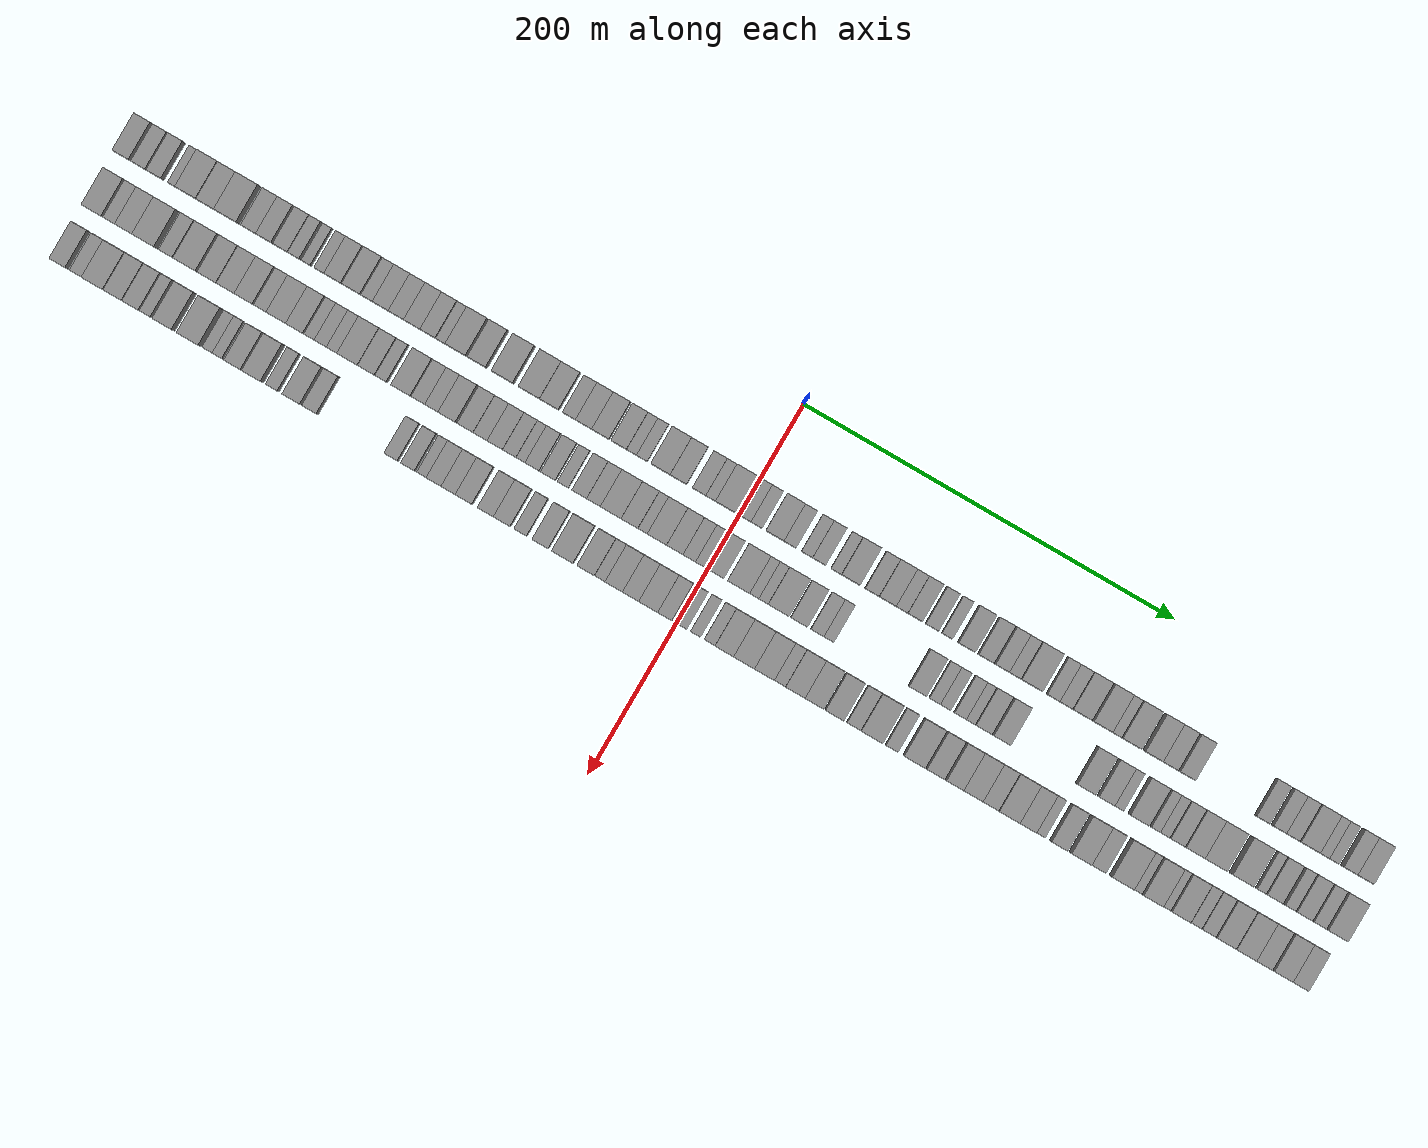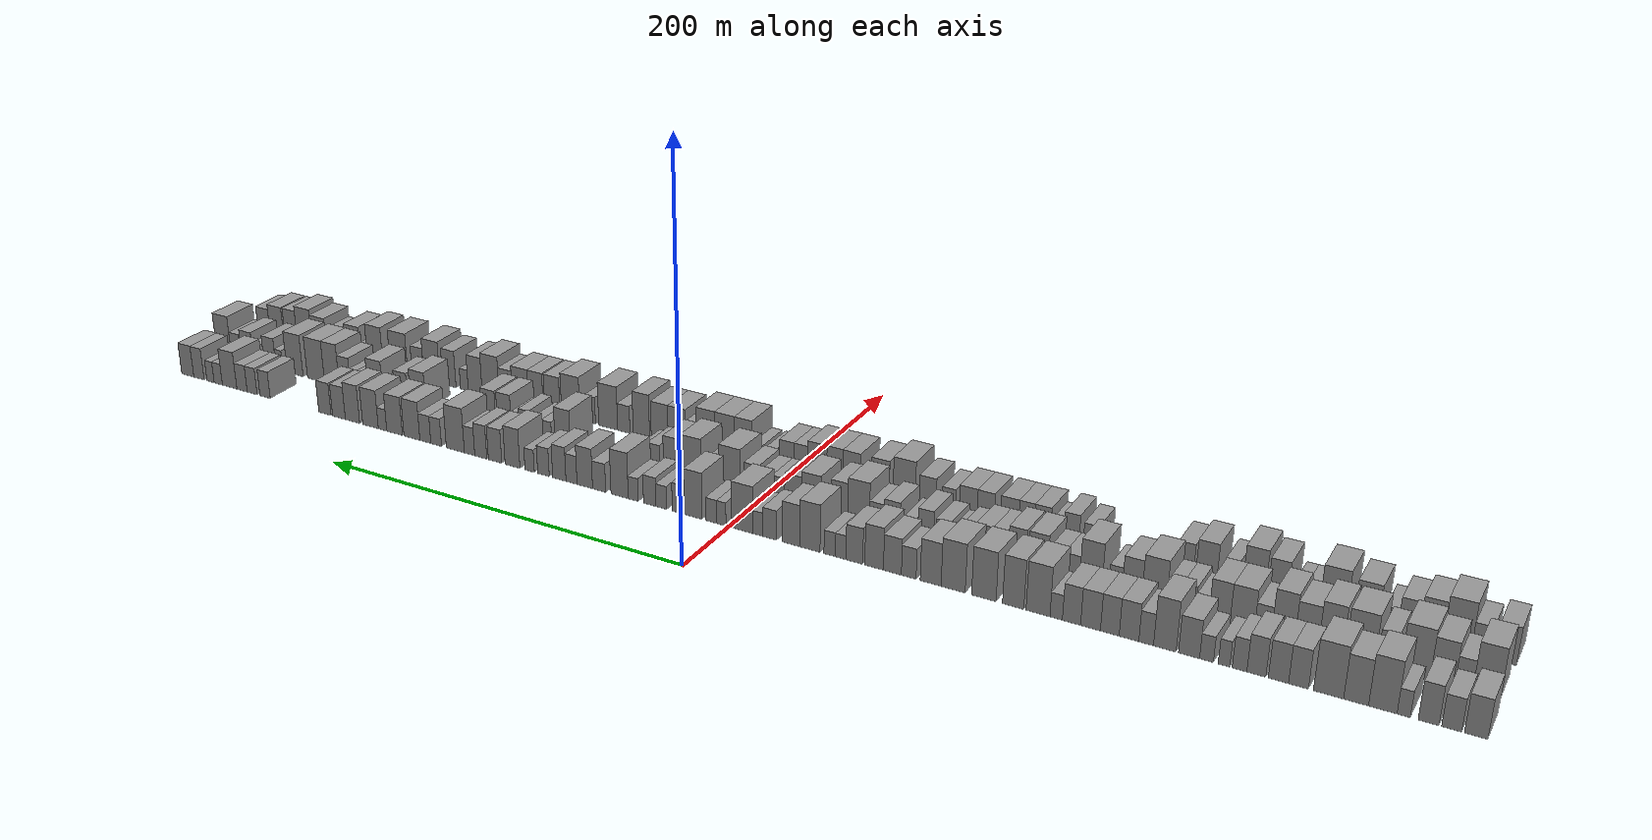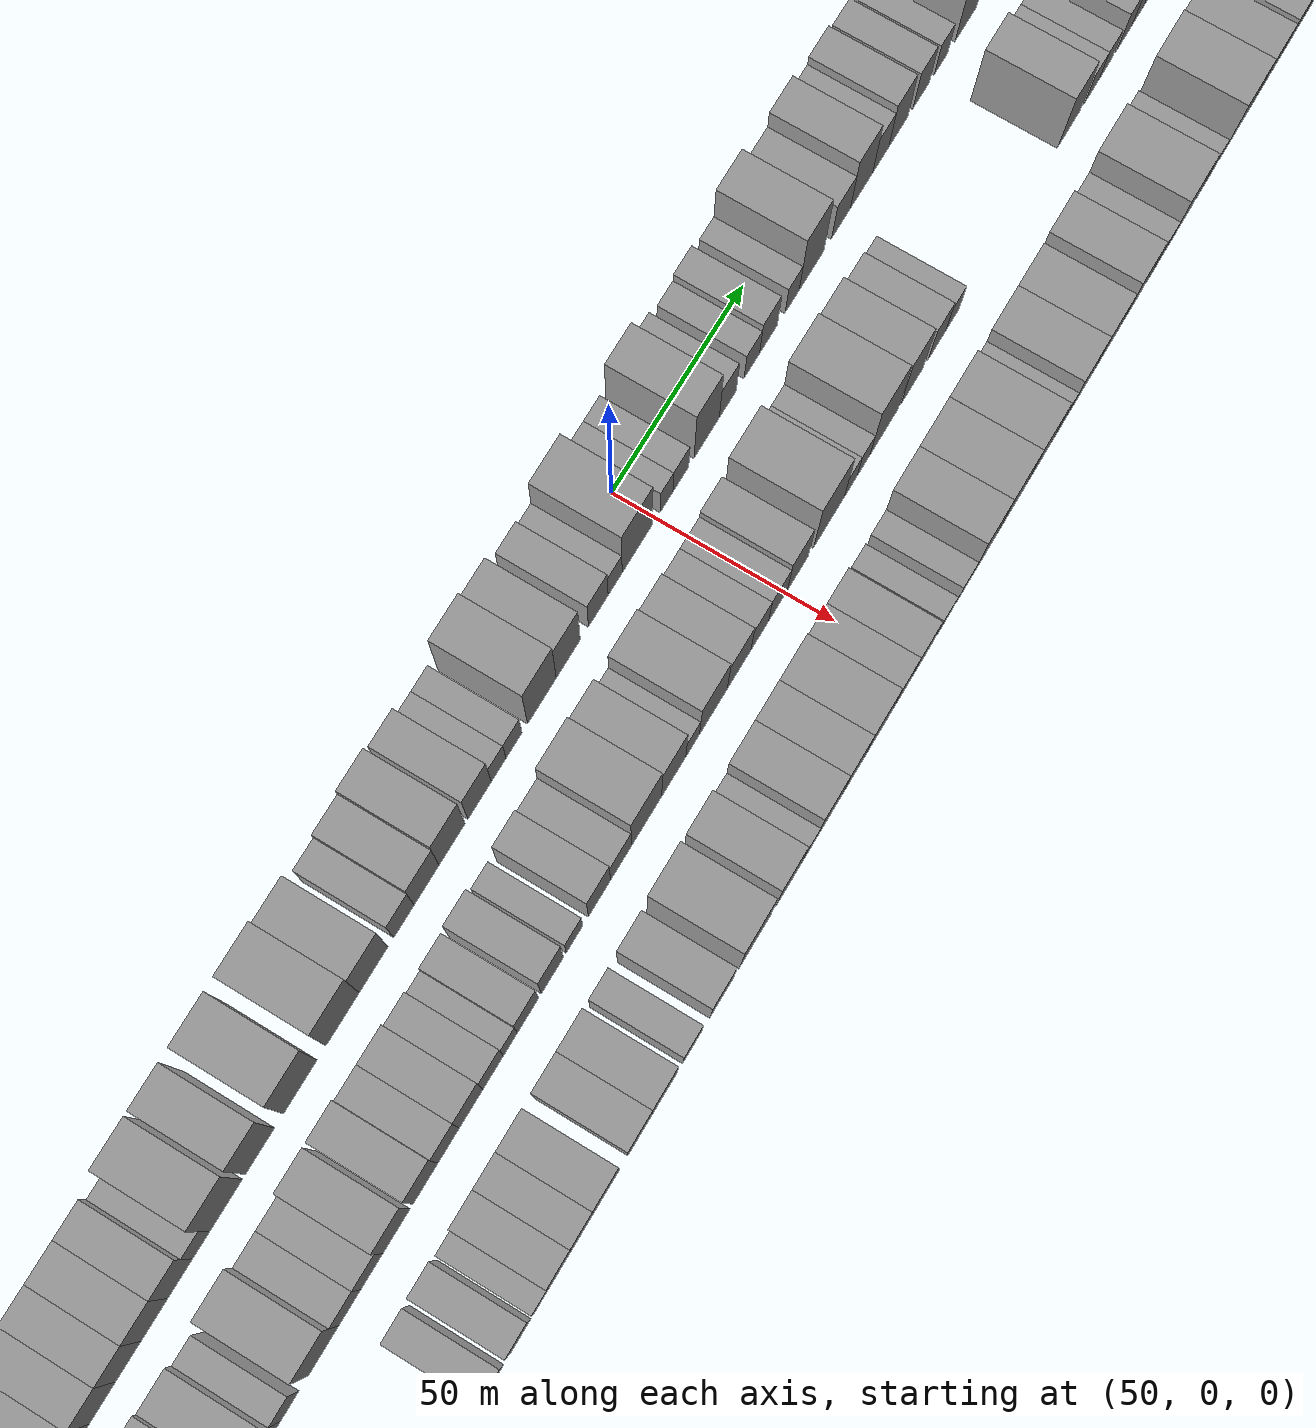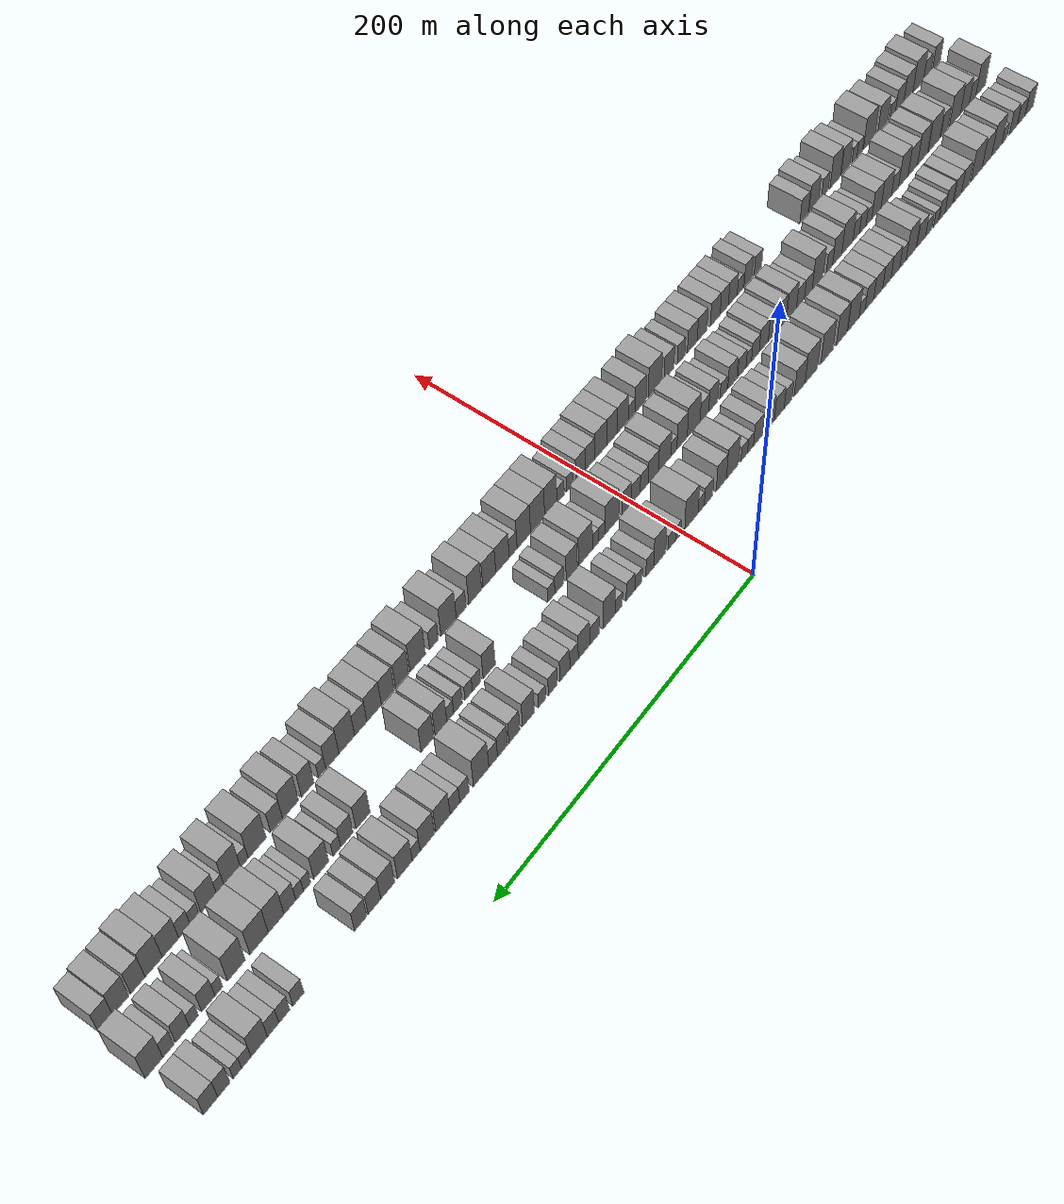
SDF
<sdf version="1.6">
 <world name="default">
  <scene>
   <sky><clouds><speed>12</speed></clouds></sky>
   <ambient>0.4 0.4 0.4 1</ambient>
   <background>0.7 0.7 0.7 1</background>
   <shadows>1</shadows>
  </scene>
  <gravity>0 0 -9.8066</gravity>
  <magnetic_field>6e-06 2.3e-05 -4.2e-05</magnetic_field>
  <physics default="0" name="default_physics" type="ode">
   <ode>
    <solver>
     <type>quick</type>
     <iters>10</iters>
     <sor>1.0</sor>
     <use_dynamic_moi_rescaling>0</use_dynamic_moi_rescaling>
    </solver>
    <constraints>
     <cfm>0</cfm>
     <erp>0.2</erp>
     <contact_max_correcting_vel>100</contact_max_correcting_vel>
     <contact_surface_layer>0.001</contact_surface_layer>
    </constraints>
   </ode>
   <max_step_size>0.004</max_step_size>
   <real_time_factor>1</real_time_factor>
   <real_time_update_rate>250</real_time_update_rate>
  </physics>
  <light name="sun" type="directional">
   <pose>0 0 10 0 0 0</pose>
   <diffuse>0.8 0.8 0.8 1</diffuse>
   <specular>0.2 0.2 0.2 1</specular>
   <attenuation>
    <range>1000</range>
    <constant>0.9</constant>
    <linear>0.01</linear>
    <quadratic>0.001</quadratic>
   </attenuation>
   <direction>-0.5 0.1 -0.9</direction>
  </light>
  <model name="building_1">
   <static>1</static>
   <pose>50.0000 -331.6397 0 0.000000 0.000000 0.000000</pose>
   <link name="link">
    <pose>0 0 9.00 0 0 0</pose>
    <collision name="collision"><geometry><box><size>20.0000 8.7205 18.0000</size></box></geometry></collision>
    <visual name="visual">
     <cast_shadows>0</cast_shadows>
     <geometry><box><size>20.0000 8.7205 18.0000</size></box></geometry>
     <material>
      <script>
       <uri>model://grey_wall/materials/scripts</uri>
       <uri>model://grey_wall/materials/textures</uri>
       <name>vrc/grey_wall</name>
      </script>
     </material>
    </visual>
   </link>
  </model>
  <model name="building_2">
   <static>1</static>
   <pose>50.0000 -322.5313 0 0.000000 0.000000 0.000000</pose>
   <link name="link">
    <pose>0 0 7.50 0 0 0</pose>
    <collision name="collision"><geometry><box><size>20.0000 7.4964 15.0000</size></box></geometry></collision>
    <visual name="visual">
     <cast_shadows>0</cast_shadows>
     <geometry><box><size>20.0000 7.4964 15.0000</size></box></geometry>
     <material>
      <script>
       <uri>model://grey_wall/materials/scripts</uri>
       <uri>model://grey_wall/materials/textures</uri>
       <name>vrc/grey_wall</name>
      </script>
     </material>
    </visual>
   </link>
  </model>
  <model name="building_3">
   <static>1</static>
   <pose>50.0000 -313.8501 0 0.000000 0.000000 0.000000</pose>
   <link name="link">
    <pose>0 0 9.00 0 0 0</pose>
    <collision name="collision"><geometry><box><size>20.0000 7.8660 18.0000</size></box></geometry></collision>
    <visual name="visual">
     <cast_shadows>0</cast_shadows>
     <geometry><box><size>20.0000 7.8660 18.0000</size></box></geometry>
     <material>
      <script>
       <uri>model://grey_wall/materials/scripts</uri>
       <uri>model://grey_wall/materials/textures</uri>
       <name>vrc/grey_wall</name>
      </script>
     </material>
    </visual>
   </link>
  </model>
  <model name="building_4">
   <static>1</static>
   <pose>50.0000 -304.3838 0 0.000000 0.000000 0.000000</pose>
   <link name="link">
    <pose>0 0 6.00 0 0 0</pose>
    <collision name="collision"><geometry><box><size>20.0000 5.0666 12.0000</size></box></geometry></collision>
    <visual name="visual">
     <cast_shadows>0</cast_shadows>
     <geometry><box><size>20.0000 5.0666 12.0000</size></box></geometry>
     <material>
      <script>
       <uri>model://grey_wall/materials/scripts</uri>
       <uri>model://grey_wall/materials/textures</uri>
       <name>vrc/grey_wall</name>
      </script>
     </material>
    </visual>
   </link>
  </model>
  <model name="building_5">
   <static>1</static>
   <pose>50.0000 -296.3426 0 0.000000 0.000000 0.000000</pose>
   <link name="link">
    <pose>0 0 12.00 0 0 0</pose>
    <collision name="collision"><geometry><box><size>20.0000 11.0157 24.0000</size></box></geometry></collision>
    <visual name="visual">
     <cast_shadows>0</cast_shadows>
     <geometry><box><size>20.0000 11.0157 24.0000</size></box></geometry>
     <material>
      <script>
       <uri>model://grey_wall/materials/scripts</uri>
       <uri>model://grey_wall/materials/textures</uri>
       <name>vrc/grey_wall</name>
      </script>
     </material>
    </visual>
   </link>
  </model>
  <model name="building_6">
   <static>1</static>
   <pose>50.0000 -285.9676 0 0.000000 0.000000 0.000000</pose>
   <link name="link">
    <pose>0 0 10.50 0 0 0</pose>
    <collision name="collision"><geometry><box><size>20.0000 9.7342 21.0000</size></box></geometry></collision>
    <visual name="visual">
     <cast_shadows>0</cast_shadows>
     <geometry><box><size>20.0000 9.7342 21.0000</size></box></geometry>
     <material>
      <script>
       <uri>model://grey_wall/materials/scripts</uri>
       <uri>model://grey_wall/materials/textures</uri>
       <name>vrc/grey_wall</name>
      </script>
     </material>
    </visual>
   </link>
  </model>
  <model name="building_7">
   <static>1</static>
   <pose>50.0000 -275.1267 0 0.000000 0.000000 0.000000</pose>
   <link name="link">
    <pose>0 0 12.00 0 0 0</pose>
    <collision name="collision"><geometry><box><size>20.0000 11.9476 24.0000</size></box></geometry></collision>
    <visual name="visual">
     <cast_shadows>0</cast_shadows>
     <geometry><box><size>20.0000 11.9476 24.0000</size></box></geometry>
     <material>
      <script>
       <uri>model://grey_wall/materials/scripts</uri>
       <uri>model://grey_wall/materials/textures</uri>
       <name>vrc/grey_wall</name>
      </script>
     </material>
    </visual>
   </link>
  </model>
  <model name="building_8">
   <static>1</static>
   <pose>50.0000 -263.1664 0 0.000000 0.000000 0.000000</pose>
   <link name="link">
    <pose>0 0 9.00 0 0 0</pose>
    <collision name="collision"><geometry><box><size>20.0000 7.9730 18.0000</size></box></geometry></collision>
    <visual name="visual">
     <cast_shadows>0</cast_shadows>
     <geometry><box><size>20.0000 7.9730 18.0000</size></box></geometry>
     <material>
      <script>
       <uri>model://grey_wall/materials/scripts</uri>
       <uri>model://grey_wall/materials/textures</uri>
       <name>vrc/grey_wall</name>
      </script>
     </material>
    </visual>
   </link>
  </model>
  <model name="building_9">
   <static>1</static>
   <pose>50.0000 -255.0837 0 0.000000 0.000000 0.000000</pose>
   <link name="link">
    <pose>0 0 9.00 0 0 0</pose>
    <collision name="collision"><geometry><box><size>20.0000 8.1924 18.0000</size></box></geometry></collision>
    <visual name="visual">
     <cast_shadows>0</cast_shadows>
     <geometry><box><size>20.0000 8.1924 18.0000</size></box></geometry>
     <material>
      <script>
       <uri>model://grey_wall/materials/scripts</uri>
       <uri>model://grey_wall/materials/textures</uri>
       <name>vrc/grey_wall</name>
      </script>
     </material>
    </visual>
   </link>
  </model>
  <model name="building_10">
   <static>1</static>
   <pose>50.0000 -246.1191 0 0.000000 0.000000 0.000000</pose>
   <link name="link">
    <pose>0 0 9.00 0 0 0</pose>
    <collision name="collision"><geometry><box><size>20.0000 7.7369 18.0000</size></box></geometry></collision>
    <visual name="visual">
     <cast_shadows>0</cast_shadows>
     <geometry><box><size>20.0000 7.7369 18.0000</size></box></geometry>
     <material>
      <script>
       <uri>model://grey_wall/materials/scripts</uri>
       <uri>model://grey_wall/materials/textures</uri>
       <name>vrc/grey_wall</name>
      </script>
     </material>
    </visual>
   </link>
  </model>
  <model name="building_11">
   <static>1</static>
   <pose>50.0000 -239.2232 0 0.000000 0.000000 0.000000</pose>
   <link name="link">
    <pose>0 0 7.50 0 0 0</pose>
    <collision name="collision"><geometry><box><size>20.0000 6.0549 15.0000</size></box></geometry></collision>
    <visual name="visual">
     <cast_shadows>0</cast_shadows>
     <geometry><box><size>20.0000 6.0549 15.0000</size></box></geometry>
     <material>
      <script>
       <uri>model://grey_wall/materials/scripts</uri>
       <uri>model://grey_wall/materials/textures</uri>
       <name>vrc/grey_wall</name>
      </script>
     </material>
    </visual>
   </link>
  </model>
  <model name="building_12">
   <static>1</static>
   <pose>50.0000 -232.7923 0 0.000000 0.000000 0.000000</pose>
   <link name="link">
    <pose>0 0 6.00 0 0 0</pose>
    <collision name="collision"><geometry><box><size>20.0000 4.8070 12.0000</size></box></geometry></collision>
    <visual name="visual">
     <cast_shadows>0</cast_shadows>
     <geometry><box><size>20.0000 4.8070 12.0000</size></box></geometry>
     <material>
      <script>
       <uri>model://grey_wall/materials/scripts</uri>
       <uri>model://grey_wall/materials/textures</uri>
       <name>vrc/grey_wall</name>
      </script>
     </material>
    </visual>
   </link>
  </model>
  <model name="building_13">
   <static>1</static>
   <pose>50.0000 -225.4865 0 0.000000 0.000000 0.000000</pose>
   <link name="link">
    <pose>0 0 6.00 0 0 0</pose>
    <collision name="collision"><geometry><box><size>20.0000 5.8045 12.0000</size></box></geometry></collision>
    <visual name="visual">
     <cast_shadows>0</cast_shadows>
     <geometry><box><size>20.0000 5.8045 12.0000</size></box></geometry>
     <material>
      <script>
       <uri>model://grey_wall/materials/scripts</uri>
       <uri>model://grey_wall/materials/textures</uri>
       <name>vrc/grey_wall</name>
      </script>
     </material>
    </visual>
   </link>
  </model>
  <model name="building_14">
   <static>1</static>
   <pose>50.0000 -218.1348 0 0.000000 0.000000 0.000000</pose>
   <link name="link">
    <pose>0 0 9.00 0 0 0</pose>
    <collision name="collision"><geometry><box><size>20.0000 8.8989 18.0000</size></box></geometry></collision>
    <visual name="visual">
     <cast_shadows>0</cast_shadows>
     <geometry><box><size>20.0000 8.8989 18.0000</size></box></geometry>
     <material>
      <script>
       <uri>model://grey_wall/materials/scripts</uri>
       <uri>model://grey_wall/materials/textures</uri>
       <name>vrc/grey_wall</name>
      </script>
     </material>
    </visual>
   </link>
  </model>
  <model name="building_15">
   <static>1</static>
   <pose>50.0000 -207.8480 0 0.000000 0.000000 0.000000</pose>
   <link name="link">
    <pose>0 0 12.00 0 0 0</pose>
    <collision name="collision"><geometry><box><size>20.0000 9.6747 24.0000</size></box></geometry></collision>
    <visual name="visual">
     <cast_shadows>0</cast_shadows>
     <geometry><box><size>20.0000 9.6747 24.0000</size></box></geometry>
     <material>
      <script>
       <uri>model://grey_wall/materials/scripts</uri>
       <uri>model://grey_wall/materials/textures</uri>
       <name>vrc/grey_wall</name>
      </script>
     </material>
    </visual>
   </link>
  </model>
  <model name="building_16">
   <static>1</static>
   <pose>50.0000 -199.8449 0 0.000000 0.000000 0.000000</pose>
   <link name="link">
    <pose>0 0 7.50 0 0 0</pose>
    <collision name="collision"><geometry><box><size>20.0000 6.3316 15.0000</size></box></geometry></collision>
    <visual name="visual">
     <cast_shadows>0</cast_shadows>
     <geometry><box><size>20.0000 6.3316 15.0000</size></box></geometry>
     <material>
      <script>
       <uri>model://grey_wall/materials/scripts</uri>
       <uri>model://grey_wall/materials/textures</uri>
       <name>vrc/grey_wall</name>
      </script>
     </material>
    </visual>
   </link>
  </model>
  <model name="building_17">
   <static>1</static>
   <pose>50.0000 -192.4107 0 0.000000 0.000000 0.000000</pose>
   <link name="link">
    <pose>0 0 9.00 0 0 0</pose>
    <collision name="collision"><geometry><box><size>20.0000 8.5367 18.0000</size></box></geometry></collision>
    <visual name="visual">
     <cast_shadows>0</cast_shadows>
     <geometry><box><size>20.0000 8.5367 18.0000</size></box></geometry>
     <material>
      <script>
       <uri>model://grey_wall/materials/scripts</uri>
       <uri>model://grey_wall/materials/textures</uri>
       <name>vrc/grey_wall</name>
      </script>
     </material>
    </visual>
   </link>
  </model>
  <model name="building_18">
   <static>1</static>
   <pose>50.0000 -184.0415 0 0.000000 0.000000 0.000000</pose>
   <link name="link">
    <pose>0 0 9.00 0 0 0</pose>
    <collision name="collision"><geometry><box><size>20.0000 8.2016 18.0000</size></box></geometry></collision>
    <visual name="visual">
     <cast_shadows>0</cast_shadows>
     <geometry><box><size>20.0000 8.2016 18.0000</size></box></geometry>
     <material>
      <script>
       <uri>model://grey_wall/materials/scripts</uri>
       <uri>model://grey_wall/materials/textures</uri>
       <name>vrc/grey_wall</name>
      </script>
     </material>
    </visual>
   </link>
  </model>
  <model name="building_19">
   <static>1</static>
   <pose>50.0000 -175.5516 0 0.000000 0.000000 0.000000</pose>
   <link name="link">
    <pose>0 0 9.00 0 0 0</pose>
    <collision name="collision"><geometry><box><size>20.0000 8.7783 18.0000</size></box></geometry></collision>
    <visual name="visual">
     <cast_shadows>0</cast_shadows>
     <geometry><box><size>20.0000 8.7783 18.0000</size></box></geometry>
     <material>
      <script>
       <uri>model://grey_wall/materials/scripts</uri>
       <uri>model://grey_wall/materials/textures</uri>
       <name>vrc/grey_wall</name>
      </script>
     </material>
    </visual>
   </link>
  </model>
  <model name="building_20">
   <static>1</static>
   <pose>50.0000 -167.0960 0 0.000000 0.000000 0.000000</pose>
   <link name="link">
    <pose>0 0 9.00 0 0 0</pose>
    <collision name="collision"><geometry><box><size>20.0000 8.1327 18.0000</size></box></geometry></collision>
    <visual name="visual">
     <cast_shadows>0</cast_shadows>
     <geometry><box><size>20.0000 8.1327 18.0000</size></box></geometry>
     <material>
      <script>
       <uri>model://grey_wall/materials/scripts</uri>
       <uri>model://grey_wall/materials/textures</uri>
       <name>vrc/grey_wall</name>
      </script>
     </material>
    </visual>
   </link>
  </model>
  <model name="building_21">
   <static>1</static>
   <pose>50.0000 -160.2294 0 0.000000 0.000000 0.000000</pose>
   <link name="link">
    <pose>0 0 6.00 0 0 0</pose>
    <collision name="collision"><geometry><box><size>20.0000 5.6006 12.0000</size></box></geometry></collision>
    <visual name="visual">
     <cast_shadows>0</cast_shadows>
     <geometry><box><size>20.0000 5.6006 12.0000</size></box></geometry>
     <material>
      <script>
       <uri>model://grey_wall/materials/scripts</uri>
       <uri>model://grey_wall/materials/textures</uri>
       <name>vrc/grey_wall</name>
      </script>
     </material>
    </visual>
   </link>
  </model>
  <model name="building_22">
   <static>1</static>
   <pose>50.0000 -151.9978 0 0.000000 0.000000 0.000000</pose>
   <link name="link">
    <pose>0 0 12.00 0 0 0</pose>
    <collision name="collision"><geometry><box><size>20.0000 10.8625 24.0000</size></box></geometry></collision>
    <visual name="visual">
     <cast_shadows>0</cast_shadows>
     <geometry><box><size>20.0000 10.8625 24.0000</size></box></geometry>
     <material>
      <script>
       <uri>model://grey_wall/materials/scripts</uri>
       <uri>model://grey_wall/materials/textures</uri>
       <name>vrc/grey_wall</name>
      </script>
     </material>
    </visual>
   </link>
  </model>
  <model name="building_23">
   <static>1</static>
   <pose>50.0000 -140.6740 0 0.000000 0.000000 0.000000</pose>
   <link name="link">
    <pose>0 0 12.00 0 0 0</pose>
    <collision name="collision"><geometry><box><size>20.0000 9.7850 24.0000</size></box></geometry></collision>
    <visual name="visual">
     <cast_shadows>0</cast_shadows>
     <geometry><box><size>20.0000 9.7850 24.0000</size></box></geometry>
     <material>
      <script>
       <uri>model://grey_wall/materials/scripts</uri>
       <uri>model://grey_wall/materials/textures</uri>
       <name>vrc/grey_wall</name>
      </script>
     </material>
    </visual>
   </link>
  </model>
  <model name="building_24">
   <static>1</static>
   <pose>50.0000 -127.0697 0 0.000000 0.000000 0.000000</pose>
   <link name="link">
    <pose>0 0 12.00 0 0 0</pose>
    <collision name="collision"><geometry><box><size>20.0000 11.4236 24.0000</size></box></geometry></collision>
    <visual name="visual">
     <cast_shadows>0</cast_shadows>
     <geometry><box><size>20.0000 11.4236 24.0000</size></box></geometry>
     <material>
      <script>
       <uri>model://grey_wall/materials/scripts</uri>
       <uri>model://grey_wall/materials/textures</uri>
       <name>vrc/grey_wall</name>
      </script>
     </material>
    </visual>
   </link>
  </model>
  <model name="building_25">
   <static>1</static>
   <pose>50.0000 -112.6428 0 0.000000 0.000000 0.000000</pose>
   <link name="link">
    <pose>0 0 12.00 0 0 0</pose>
    <collision name="collision"><geometry><box><size>20.0000 11.4302 24.0000</size></box></geometry></collision>
    <visual name="visual">
     <cast_shadows>0</cast_shadows>
     <geometry><box><size>20.0000 11.4302 24.0000</size></box></geometry>
     <material>
      <script>
       <uri>model://grey_wall/materials/scripts</uri>
       <uri>model://grey_wall/materials/textures</uri>
       <name>vrc/grey_wall</name>
      </script>
     </material>
    </visual>
   </link>
  </model>
  <model name="building_26">
   <static>1</static>
   <pose>50.0000 -101.9458 0 0.000000 0.000000 0.000000</pose>
   <link name="link">
    <pose>0 0 10.50 0 0 0</pose>
    <collision name="collision"><geometry><box><size>20.0000 9.9638 21.0000</size></box></geometry></collision>
    <visual name="visual">
     <cast_shadows>0</cast_shadows>
     <geometry><box><size>20.0000 9.9638 21.0000</size></box></geometry>
     <material>
      <script>
       <uri>model://grey_wall/materials/scripts</uri>
       <uri>model://grey_wall/materials/textures</uri>
       <name>vrc/grey_wall</name>
      </script>
     </material>
    </visual>
   </link>
  </model>
  <model name="building_27">
   <static>1</static>
   <pose>50.0000 -91.4111 0 0.000000 0.000000 0.000000</pose>
   <link name="link">
    <pose>0 0 7.50 0 0 0</pose>
    <collision name="collision"><geometry><box><size>20.0000 7.1054 15.0000</size></box></geometry></collision>
    <visual name="visual">
     <cast_shadows>0</cast_shadows>
     <geometry><box><size>20.0000 7.1054 15.0000</size></box></geometry>
     <material>
      <script>
       <uri>model://grey_wall/materials/scripts</uri>
       <uri>model://grey_wall/materials/textures</uri>
       <name>vrc/grey_wall</name>
      </script>
     </material>
    </visual>
   </link>
  </model>
  <model name="building_28">
   <static>1</static>
   <pose>50.0000 -83.4727 0 0.000000 0.000000 0.000000</pose>
   <link name="link">
    <pose>0 0 9.00 0 0 0</pose>
    <collision name="collision"><geometry><box><size>20.0000 8.7715 18.0000</size></box></geometry></collision>
    <visual name="visual">
     <cast_shadows>0</cast_shadows>
     <geometry><box><size>20.0000 8.7715 18.0000</size></box></geometry>
     <material>
      <script>
       <uri>model://grey_wall/materials/scripts</uri>
       <uri>model://grey_wall/materials/textures</uri>
       <name>vrc/grey_wall</name>
      </script>
     </material>
    </visual>
   </link>
  </model>
  <model name="building_29">
   <static>1</static>
   <pose>50.0000 -74.4863 0 0.000000 0.000000 0.000000</pose>
   <link name="link">
    <pose>0 0 10.50 0 0 0</pose>
    <collision name="collision"><geometry><box><size>20.0000 9.2012 21.0000</size></box></geometry></collision>
    <visual name="visual">
     <cast_shadows>0</cast_shadows>
     <geometry><box><size>20.0000 9.2012 21.0000</size></box></geometry>
     <material>
      <script>
       <uri>model://grey_wall/materials/scripts</uri>
       <uri>model://grey_wall/materials/textures</uri>
       <name>vrc/grey_wall</name>
      </script>
     </material>
    </visual>
   </link>
  </model>
  <model name="building_30">
   <static>1</static>
   <pose>50.0000 -64.7141 0 0.000000 0.000000 0.000000</pose>
   <link name="link">
    <pose>0 0 9.00 0 0 0</pose>
    <collision name="collision"><geometry><box><size>20.0000 8.3432 18.0000</size></box></geometry></collision>
    <visual name="visual">
     <cast_shadows>0</cast_shadows>
     <geometry><box><size>20.0000 8.3432 18.0000</size></box></geometry>
     <material>
      <script>
       <uri>model://grey_wall/materials/scripts</uri>
       <uri>model://grey_wall/materials/textures</uri>
       <name>vrc/grey_wall</name>
      </script>
     </material>
    </visual>
   </link>
  </model>
  <model name="building_31">
   <static>1</static>
   <pose>50.0000 -57.9060 0 0.000000 0.000000 0.000000</pose>
   <link name="link">
    <pose>0 0 6.00 0 0 0</pose>
    <collision name="collision"><geometry><box><size>20.0000 5.2730 12.0000</size></box></geometry></collision>
    <visual name="visual">
     <cast_shadows>0</cast_shadows>
     <geometry><box><size>20.0000 5.2730 12.0000</size></box></geometry>
     <material>
      <script>
       <uri>model://grey_wall/materials/scripts</uri>
       <uri>model://grey_wall/materials/textures</uri>
       <name>vrc/grey_wall</name>
      </script>
     </material>
    </visual>
   </link>
  </model>
  <model name="building_32">
   <static>1</static>
   <pose>50.0000 -52.3699 0 0.000000 0.000000 0.000000</pose>
   <link name="link">
    <pose>0 0 6.00 0 0 0</pose>
    <collision name="collision"><geometry><box><size>20.0000 5.7993 12.0000</size></box></geometry></collision>
    <visual name="visual">
     <cast_shadows>0</cast_shadows>
     <geometry><box><size>20.0000 5.7993 12.0000</size></box></geometry>
     <material>
      <script>
       <uri>model://grey_wall/materials/scripts</uri>
       <uri>model://grey_wall/materials/textures</uri>
       <name>vrc/grey_wall</name>
      </script>
     </material>
    </visual>
   </link>
  </model>
  <model name="building_33">
   <static>1</static>
   <pose>50.0000 -42.2846 0 0.000000 0.000000 0.000000</pose>
   <link name="link">
    <pose>0 0 12.00 0 0 0</pose>
    <collision name="collision"><geometry><box><size>20.0000 10.3713 24.0000</size></box></geometry></collision>
    <visual name="visual">
     <cast_shadows>0</cast_shadows>
     <geometry><box><size>20.0000 10.3713 24.0000</size></box></geometry>
     <material>
      <script>
       <uri>model://grey_wall/materials/scripts</uri>
       <uri>model://grey_wall/materials/textures</uri>
       <name>vrc/grey_wall</name>
      </script>
     </material>
    </visual>
   </link>
  </model>
  <model name="building_34">
   <static>1</static>
   <pose>50.0000 -32.6914 0 0.000000 0.000000 0.000000</pose>
   <link name="link">
    <pose>0 0 10.50 0 0 0</pose>
    <collision name="collision"><geometry><box><size>20.0000 8.8151 21.0000</size></box></geometry></collision>
    <visual name="visual">
     <cast_shadows>0</cast_shadows>
     <geometry><box><size>20.0000 8.8151 21.0000</size></box></geometry>
     <material>
      <script>
       <uri>model://grey_wall/materials/scripts</uri>
       <uri>model://grey_wall/materials/textures</uri>
       <name>vrc/grey_wall</name>
      </script>
     </material>
    </visual>
   </link>
  </model>
  <model name="building_35">
   <static>1</static>
   <pose>50.0000 -21.6587 0 0.000000 0.000000 0.000000</pose>
   <link name="link">
    <pose>0 0 7.50 0 0 0</pose>
    <collision name="collision"><geometry><box><size>20.0000 7.2503 15.0000</size></box></geometry></collision>
    <visual name="visual">
     <cast_shadows>0</cast_shadows>
     <geometry><box><size>20.0000 7.2503 15.0000</size></box></geometry>
     <material>
      <script>
       <uri>model://grey_wall/materials/scripts</uri>
       <uri>model://grey_wall/materials/textures</uri>
       <name>vrc/grey_wall</name>
      </script>
     </material>
    </visual>
   </link>
  </model>
  <model name="building_36">
   <static>1</static>
   <pose>50.0000 -15.4284 0 0.000000 0.000000 0.000000</pose>
   <link name="link">
    <pose>0 0 6.00 0 0 0</pose>
    <collision name="collision"><geometry><box><size>20.0000 5.2104 12.0000</size></box></geometry></collision>
    <visual name="visual">
     <cast_shadows>0</cast_shadows>
     <geometry><box><size>20.0000 5.2104 12.0000</size></box></geometry>
     <material>
      <script>
       <uri>model://grey_wall/materials/scripts</uri>
       <uri>model://grey_wall/materials/textures</uri>
       <name>vrc/grey_wall</name>
      </script>
     </material>
    </visual>
   </link>
  </model>
  <model name="building_37">
   <static>1</static>
   <pose>50.0000 -7.2156 0 0.000000 0.000000 0.000000</pose>
   <link name="link">
    <pose>0 0 12.00 0 0 0</pose>
    <collision name="collision"><geometry><box><size>20.0000 11.2152 24.0000</size></box></geometry></collision>
    <visual name="visual">
     <cast_shadows>0</cast_shadows>
     <geometry><box><size>20.0000 11.2152 24.0000</size></box></geometry>
     <material>
      <script>
       <uri>model://grey_wall/materials/scripts</uri>
       <uri>model://grey_wall/materials/textures</uri>
       <name>vrc/grey_wall</name>
      </script>
     </material>
    </visual>
   </link>
  </model>
  <model name="building_38">
   <static>1</static>
   <pose>50.0000 3.7937 0 0.000000 0.000000 0.000000</pose>
   <link name="link">
    <pose>0 0 6.00 0 0 0</pose>
    <collision name="collision"><geometry><box><size>20.0000 4.8033 12.0000</size></box></geometry></collision>
    <visual name="visual">
     <cast_shadows>0</cast_shadows>
     <geometry><box><size>20.0000 4.8033 12.0000</size></box></geometry>
     <material>
      <script>
       <uri>model://grey_wall/materials/scripts</uri>
       <uri>model://grey_wall/materials/textures</uri>
       <name>vrc/grey_wall</name>
      </script>
     </material>
    </visual>
   </link>
  </model>
  <model name="building_39">
   <static>1</static>
   <pose>50.0000 9.1888 0 0.000000 0.000000 0.000000</pose>
   <link name="link">
    <pose>0 0 6.00 0 0 0</pose>
    <collision name="collision"><geometry><box><size>20.0000 5.9868 12.0000</size></box></geometry></collision>
    <visual name="visual">
     <cast_shadows>0</cast_shadows>
     <geometry><box><size>20.0000 5.9868 12.0000</size></box></geometry>
     <material>
      <script>
       <uri>model://grey_wall/materials/scripts</uri>
       <uri>model://grey_wall/materials/textures</uri>
       <name>vrc/grey_wall</name>
      </script>
     </material>
    </visual>
   </link>
  </model>
  <model name="building_40">
   <static>1</static>
   <pose>50.0000 18.9999 0 0.000000 0.000000 0.000000</pose>
   <link name="link">
    <pose>0 0 12.00 0 0 0</pose>
    <collision name="collision"><geometry><box><size>20.0000 9.6355 24.0000</size></box></geometry></collision>
    <visual name="visual">
     <cast_shadows>0</cast_shadows>
     <geometry><box><size>20.0000 9.6355 24.0000</size></box></geometry>
     <material>
      <script>
       <uri>model://grey_wall/materials/scripts</uri>
       <uri>model://grey_wall/materials/textures</uri>
       <name>vrc/grey_wall</name>
      </script>
     </material>
    </visual>
   </link>
  </model>
  <model name="building_41">
   <static>1</static>
   <pose>50.0000 27.0947 0 0.000000 0.000000 0.000000</pose>
   <link name="link">
    <pose>0 0 7.50 0 0 0</pose>
    <collision name="collision"><geometry><box><size>20.0000 6.5542 15.0000</size></box></geometry></collision>
    <visual name="visual">
     <cast_shadows>0</cast_shadows>
     <geometry><box><size>20.0000 6.5542 15.0000</size></box></geometry>
     <material>
      <script>
       <uri>model://grey_wall/materials/scripts</uri>
       <uri>model://grey_wall/materials/textures</uri>
       <name>vrc/grey_wall</name>
      </script>
     </material>
    </visual>
   </link>
  </model>
  <model name="building_42">
   <static>1</static>
   <pose>50.0000 36.3470 0 0.000000 0.000000 0.000000</pose>
   <link name="link">
    <pose>0 0 6.00 0 0 0</pose>
    <collision name="collision"><geometry><box><size>20.0000 5.9503 12.0000</size></box></geometry></collision>
    <visual name="visual">
     <cast_shadows>0</cast_shadows>
     <geometry><box><size>20.0000 5.9503 12.0000</size></box></geometry>
     <material>
      <script>
       <uri>model://grey_wall/materials/scripts</uri>
       <uri>model://grey_wall/materials/textures</uri>
       <name>vrc/grey_wall</name>
      </script>
     </material>
    </visual>
   </link>
  </model>
  <model name="building_43">
   <static>1</static>
   <pose>50.0000 42.7750 0 0.000000 0.000000 0.000000</pose>
   <link name="link">
    <pose>0 0 7.50 0 0 0</pose>
    <collision name="collision"><geometry><box><size>20.0000 6.9056 15.0000</size></box></geometry></collision>
    <visual name="visual">
     <cast_shadows>0</cast_shadows>
     <geometry><box><size>20.0000 6.9056 15.0000</size></box></geometry>
     <material>
      <script>
       <uri>model://grey_wall/materials/scripts</uri>
       <uri>model://grey_wall/materials/textures</uri>
       <name>vrc/grey_wall</name>
      </script>
     </material>
    </visual>
   </link>
  </model>
  <model name="building_44">
   <static>1</static>
   <pose>50.0000 51.9969 0 0.000000 0.000000 0.000000</pose>
   <link name="link">
    <pose>0 0 6.00 0 0 0</pose>
    <collision name="collision"><geometry><box><size>20.0000 5.5381 12.0000</size></box></geometry></collision>
    <visual name="visual">
     <cast_shadows>0</cast_shadows>
     <geometry><box><size>20.0000 5.5381 12.0000</size></box></geometry>
     <material>
      <script>
       <uri>model://grey_wall/materials/scripts</uri>
       <uri>model://grey_wall/materials/textures</uri>
       <name>vrc/grey_wall</name>
      </script>
     </material>
    </visual>
   </link>
  </model>
  <model name="building_45">
   <static>1</static>
   <pose>50.0000 59.6336 0 0.000000 0.000000 0.000000</pose>
   <link name="link">
    <pose>0 0 12.00 0 0 0</pose>
    <collision name="collision"><geometry><box><size>20.0000 9.7353 24.0000</size></box></geometry></collision>
    <visual name="visual">
     <cast_shadows>0</cast_shadows>
     <geometry><box><size>20.0000 9.7353 24.0000</size></box></geometry>
     <material>
      <script>
       <uri>model://grey_wall/materials/scripts</uri>
       <uri>model://grey_wall/materials/textures</uri>
       <name>vrc/grey_wall</name>
      </script>
     </material>
    </visual>
   </link>
  </model>
  <model name="building_46">
   <static>1</static>
   <pose>50.0000 71.2349 0 0.000000 0.000000 0.000000</pose>
   <link name="link">
    <pose>0 0 7.50 0 0 0</pose>
    <collision name="collision"><geometry><box><size>20.0000 7.4674 15.0000</size></box></geometry></collision>
    <visual name="visual">
     <cast_shadows>0</cast_shadows>
     <geometry><box><size>20.0000 7.4674 15.0000</size></box></geometry>
     <material>
      <script>
       <uri>model://grey_wall/materials/scripts</uri>
       <uri>model://grey_wall/materials/textures</uri>
       <name>vrc/grey_wall</name>
      </script>
     </material>
    </visual>
   </link>
  </model>
  <model name="building_47">
   <static>1</static>
   <pose>50.0000 79.4312 0 0.000000 0.000000 0.000000</pose>
   <link name="link">
    <pose>0 0 10.50 0 0 0</pose>
    <collision name="collision"><geometry><box><size>20.0000 8.9253 21.0000</size></box></geometry></collision>
    <visual name="visual">
     <cast_shadows>0</cast_shadows>
     <geometry><box><size>20.0000 8.9253 21.0000</size></box></geometry>
     <material>
      <script>
       <uri>model://grey_wall/materials/scripts</uri>
       <uri>model://grey_wall/materials/textures</uri>
       <name>vrc/grey_wall</name>
      </script>
     </material>
    </visual>
   </link>
  </model>
  <model name="building_48">
   <static>1</static>
   <pose>50.0000 87.1075 0 0.000000 0.000000 0.000000</pose>
   <link name="link">
    <pose>0 0 7.50 0 0 0</pose>
    <collision name="collision"><geometry><box><size>20.0000 6.4273 15.0000</size></box></geometry></collision>
    <visual name="visual">
     <cast_shadows>0</cast_shadows>
     <geometry><box><size>20.0000 6.4273 15.0000</size></box></geometry>
     <material>
      <script>
       <uri>model://grey_wall/materials/scripts</uri>
       <uri>model://grey_wall/materials/textures</uri>
       <name>vrc/grey_wall</name>
      </script>
     </material>
    </visual>
   </link>
  </model>
  <model name="building_49">
   <static>1</static>
   <pose>50.0000 94.1932 0 0.000000 0.000000 0.000000</pose>
   <link name="link">
    <pose>0 0 9.00 0 0 0</pose>
    <collision name="collision"><geometry><box><size>20.0000 7.7441 18.0000</size></box></geometry></collision>
    <visual name="visual">
     <cast_shadows>0</cast_shadows>
     <geometry><box><size>20.0000 7.7441 18.0000</size></box></geometry>
     <material>
      <script>
       <uri>model://grey_wall/materials/scripts</uri>
       <uri>model://grey_wall/materials/textures</uri>
       <name>vrc/grey_wall</name>
      </script>
     </material>
    </visual>
   </link>
  </model>
  <model name="building_50">
   <static>1</static>
   <pose>50.0000 103.4503 0 0.000000 0.000000 0.000000</pose>
   <link name="link">
    <pose>0 0 7.50 0 0 0</pose>
    <collision name="collision"><geometry><box><size>20.0000 6.7701 15.0000</size></box></geometry></collision>
    <visual name="visual">
     <cast_shadows>0</cast_shadows>
     <geometry><box><size>20.0000 6.7701 15.0000</size></box></geometry>
     <material>
      <script>
       <uri>model://grey_wall/materials/scripts</uri>
       <uri>model://grey_wall/materials/textures</uri>
       <name>vrc/grey_wall</name>
      </script>
     </material>
    </visual>
   </link>
  </model>
  <model name="building_51">
   <static>1</static>
   <pose>50.0000 111.6134 0 0.000000 0.000000 0.000000</pose>
   <link name="link">
    <pose>0 0 6.00 0 0 0</pose>
    <collision name="collision"><geometry><box><size>20.0000 5.5561 12.0000</size></box></geometry></collision>
    <visual name="visual">
     <cast_shadows>0</cast_shadows>
     <geometry><box><size>20.0000 5.5561 12.0000</size></box></geometry>
     <material>
      <script>
       <uri>model://grey_wall/materials/scripts</uri>
       <uri>model://grey_wall/materials/textures</uri>
       <name>vrc/grey_wall</name>
      </script>
     </material>
    </visual>
   </link>
  </model>
  <model name="building_52">
   <static>1</static>
   <pose>50.0000 121.8254 0 0.000000 0.000000 0.000000</pose>
   <link name="link">
    <pose>0 0 10.50 0 0 0</pose>
    <collision name="collision"><geometry><box><size>20.0000 8.8678 21.0000</size></box></geometry></collision>
    <visual name="visual">
     <cast_shadows>0</cast_shadows>
     <geometry><box><size>20.0000 8.8678 21.0000</size></box></geometry>
     <material>
      <script>
       <uri>model://grey_wall/materials/scripts</uri>
       <uri>model://grey_wall/materials/textures</uri>
       <name>vrc/grey_wall</name>
      </script>
     </material>
    </visual>
   </link>
  </model>
  <model name="building_53">
   <static>1</static>
   <pose>50.0000 132.2861 0 0.000000 0.000000 0.000000</pose>
   <link name="link">
    <pose>0 0 9.00 0 0 0</pose>
    <collision name="collision"><geometry><box><size>20.0000 8.0538 18.0000</size></box></geometry></collision>
    <visual name="visual">
     <cast_shadows>0</cast_shadows>
     <geometry><box><size>20.0000 8.0538 18.0000</size></box></geometry>
     <material>
      <script>
       <uri>model://grey_wall/materials/scripts</uri>
       <uri>model://grey_wall/materials/textures</uri>
       <name>vrc/grey_wall</name>
      </script>
     </material>
    </visual>
   </link>
  </model>
  <model name="building_54">
   <static>1</static>
   <pose>50.0000 140.9783 0 0.000000 0.000000 0.000000</pose>
   <link name="link">
    <pose>0 0 9.00 0 0 0</pose>
    <collision name="collision"><geometry><box><size>20.0000 7.3305 18.0000</size></box></geometry></collision>
    <visual name="visual">
     <cast_shadows>0</cast_shadows>
     <geometry><box><size>20.0000 7.3305 18.0000</size></box></geometry>
     <material>
      <script>
       <uri>model://grey_wall/materials/scripts</uri>
       <uri>model://grey_wall/materials/textures</uri>
       <name>vrc/grey_wall</name>
      </script>
     </material>
    </visual>
   </link>
  </model>
  <model name="building_55">
   <static>1</static>
   <pose>50.0000 147.8227 0 0.000000 0.000000 0.000000</pose>
   <link name="link">
    <pose>0 0 7.50 0 0 0</pose>
    <collision name="collision"><geometry><box><size>20.0000 6.3583 15.0000</size></box></geometry></collision>
    <visual name="visual">
     <cast_shadows>0</cast_shadows>
     <geometry><box><size>20.0000 6.3583 15.0000</size></box></geometry>
     <material>
      <script>
       <uri>model://grey_wall/materials/scripts</uri>
       <uri>model://grey_wall/materials/textures</uri>
       <name>vrc/grey_wall</name>
      </script>
     </material>
    </visual>
   </link>
  </model>
  <model name="building_56">
   <static>1</static>
   <pose>50.0000 156.5805 0 0.000000 0.000000 0.000000</pose>
   <link name="link">
    <pose>0 0 12.00 0 0 0</pose>
    <collision name="collision"><geometry><box><size>20.0000 11.1573 24.0000</size></box></geometry></collision>
    <visual name="visual">
     <cast_shadows>0</cast_shadows>
     <geometry><box><size>20.0000 11.1573 24.0000</size></box></geometry>
     <material>
      <script>
       <uri>model://grey_wall/materials/scripts</uri>
       <uri>model://grey_wall/materials/textures</uri>
       <name>vrc/grey_wall</name>
      </script>
     </material>
    </visual>
   </link>
  </model>
  <model name="building_57">
   <static>1</static>
   <pose>50.0000 168.4880 0 0.000000 0.000000 0.000000</pose>
   <link name="link">
    <pose>0 0 7.50 0 0 0</pose>
    <collision name="collision"><geometry><box><size>20.0000 6.6577 15.0000</size></box></geometry></collision>
    <visual name="visual">
     <cast_shadows>0</cast_shadows>
     <geometry><box><size>20.0000 6.6577 15.0000</size></box></geometry>
     <material>
      <script>
       <uri>model://grey_wall/materials/scripts</uri>
       <uri>model://grey_wall/materials/textures</uri>
       <name>vrc/grey_wall</name>
      </script>
     </material>
    </visual>
   </link>
  </model>
  <model name="building_58">
   <static>1</static>
   <pose>50.0000 175.2801 0 0.000000 0.000000 0.000000</pose>
   <link name="link">
    <pose>0 0 7.50 0 0 0</pose>
    <collision name="collision"><geometry><box><size>20.0000 6.9265 15.0000</size></box></geometry></collision>
    <visual name="visual">
     <cast_shadows>0</cast_shadows>
     <geometry><box><size>20.0000 6.9265 15.0000</size></box></geometry>
     <material>
      <script>
       <uri>model://grey_wall/materials/scripts</uri>
       <uri>model://grey_wall/materials/textures</uri>
       <name>vrc/grey_wall</name>
      </script>
     </material>
    </visual>
   </link>
  </model>
  <model name="building_59">
   <static>1</static>
   <pose>50.0000 183.7782 0 0.000000 0.000000 0.000000</pose>
   <link name="link">
    <pose>0 0 10.50 0 0 0</pose>
    <collision name="collision"><geometry><box><size>20.0000 10.0697 21.0000</size></box></geometry></collision>
    <visual name="visual">
     <cast_shadows>0</cast_shadows>
     <geometry><box><size>20.0000 10.0697 21.0000</size></box></geometry>
     <material>
      <script>
       <uri>model://grey_wall/materials/scripts</uri>
       <uri>model://grey_wall/materials/textures</uri>
       <name>vrc/grey_wall</name>
      </script>
     </material>
    </visual>
   </link>
  </model>
  <model name="building_60">
   <static>1</static>
   <pose>50.0000 194.8084 0 0.000000 0.000000 0.000000</pose>
   <link name="link">
    <pose>0 0 10.50 0 0 0</pose>
    <collision name="collision"><geometry><box><size>20.0000 9.9906 21.0000</size></box></geometry></collision>
    <visual name="visual">
     <cast_shadows>0</cast_shadows>
     <geometry><box><size>20.0000 9.9906 21.0000</size></box></geometry>
     <material>
      <script>
       <uri>model://grey_wall/materials/scripts</uri>
       <uri>model://grey_wall/materials/textures</uri>
       <name>vrc/grey_wall</name>
      </script>
     </material>
    </visual>
   </link>
  </model>
  <model name="building_61">
   <static>1</static>
   <pose>50.0000 202.5305 0 0.000000 0.000000 0.000000</pose>
   <link name="link">
    <pose>0 0 6.00 0 0 0</pose>
    <collision name="collision"><geometry><box><size>20.0000 5.4536 12.0000</size></box></geometry></collision>
    <visual name="visual">
     <cast_shadows>0</cast_shadows>
     <geometry><box><size>20.0000 5.4536 12.0000</size></box></geometry>
     <material>
      <script>
       <uri>model://grey_wall/materials/scripts</uri>
       <uri>model://grey_wall/materials/textures</uri>
       <name>vrc/grey_wall</name>
      </script>
     </material>
    </visual>
   </link>
  </model>
  <model name="building_62">
   <static>1</static>
   <pose>50.0000 210.3117 0 0.000000 0.000000 0.000000</pose>
   <link name="link">
    <pose>0 0 10.50 0 0 0</pose>
    <collision name="collision"><geometry><box><size>20.0000 10.1088 21.0000</size></box></geometry></collision>
    <visual name="visual">
     <cast_shadows>0</cast_shadows>
     <geometry><box><size>20.0000 10.1088 21.0000</size></box></geometry>
     <material>
      <script>
       <uri>model://grey_wall/materials/scripts</uri>
       <uri>model://grey_wall/materials/textures</uri>
       <name>vrc/grey_wall</name>
      </script>
     </material>
    </visual>
   </link>
  </model>
  <model name="building_63">
   <static>1</static>
   <pose>50.0000 222.0658 0 0.000000 0.000000 0.000000</pose>
   <link name="link">
    <pose>0 0 10.50 0 0 0</pose>
    <collision name="collision"><geometry><box><size>20.0000 9.3994 21.0000</size></box></geometry></collision>
    <visual name="visual">
     <cast_shadows>0</cast_shadows>
     <geometry><box><size>20.0000 9.3994 21.0000</size></box></geometry>
     <material>
      <script>
       <uri>model://grey_wall/materials/scripts</uri>
       <uri>model://grey_wall/materials/textures</uri>
       <name>vrc/grey_wall</name>
      </script>
     </material>
    </visual>
   </link>
  </model>
  <model name="building_64">
   <static>1</static>
   <pose>50.0000 230.9824 0 0.000000 0.000000 0.000000</pose>
   <link name="link">
    <pose>0 0 9.00 0 0 0</pose>
    <collision name="collision"><geometry><box><size>20.0000 8.4338 18.0000</size></box></geometry></collision>
    <visual name="visual">
     <cast_shadows>0</cast_shadows>
     <geometry><box><size>20.0000 8.4338 18.0000</size></box></geometry>
     <material>
      <script>
       <uri>model://grey_wall/materials/scripts</uri>
       <uri>model://grey_wall/materials/textures</uri>
       <name>vrc/grey_wall</name>
      </script>
     </material>
    </visual>
   </link>
  </model>
  <model name="building_65">
   <static>1</static>
   <pose>50.0000 240.2731 0 0.000000 0.000000 0.000000</pose>
   <link name="link">
    <pose>0 0 9.00 0 0 0</pose>
    <collision name="collision"><geometry><box><size>20.0000 8.1475 18.0000</size></box></geometry></collision>
    <visual name="visual">
     <cast_shadows>0</cast_shadows>
     <geometry><box><size>20.0000 8.1475 18.0000</size></box></geometry>
     <material>
      <script>
       <uri>model://grey_wall/materials/scripts</uri>
       <uri>model://grey_wall/materials/textures</uri>
       <name>vrc/grey_wall</name>
      </script>
     </material>
    </visual>
   </link>
  </model>
  <model name="building_66">
   <static>1</static>
   <pose>50.0000 280.9391 0 0.000000 0.000000 0.000000</pose>
   <link name="link">
    <pose>0 0 7.50 0 0 0</pose>
    <collision name="collision"><geometry><box><size>20.0000 7.0615 15.0000</size></box></geometry></collision>
    <visual name="visual">
     <cast_shadows>0</cast_shadows>
     <geometry><box><size>20.0000 7.0615 15.0000</size></box></geometry>
     <material>
      <script>
       <uri>model://grey_wall/materials/scripts</uri>
       <uri>model://grey_wall/materials/textures</uri>
       <name>vrc/grey_wall</name>
      </script>
     </material>
    </visual>
   </link>
  </model>
  <model name="building_67">
   <static>1</static>
   <pose>50.0000 289.9208 0 0.000000 0.000000 0.000000</pose>
   <link name="link">
    <pose>0 0 7.50 0 0 0</pose>
    <collision name="collision"><geometry><box><size>20.0000 6.9018 15.0000</size></box></geometry></collision>
    <visual name="visual">
     <cast_shadows>0</cast_shadows>
     <geometry><box><size>20.0000 6.9018 15.0000</size></box></geometry>
     <material>
      <script>
       <uri>model://grey_wall/materials/scripts</uri>
       <uri>model://grey_wall/materials/textures</uri>
       <name>vrc/grey_wall</name>
      </script>
     </material>
    </visual>
   </link>
  </model>
  <model name="building_68">
   <static>1</static>
   <pose>50.0000 296.9847 0 0.000000 0.000000 0.000000</pose>
   <link name="link">
    <pose>0 0 7.50 0 0 0</pose>
    <collision name="collision"><geometry><box><size>20.0000 7.2260 15.0000</size></box></geometry></collision>
    <visual name="visual">
     <cast_shadows>0</cast_shadows>
     <geometry><box><size>20.0000 7.2260 15.0000</size></box></geometry>
     <material>
      <script>
       <uri>model://grey_wall/materials/scripts</uri>
       <uri>model://grey_wall/materials/textures</uri>
       <name>vrc/grey_wall</name>
      </script>
     </material>
    </visual>
   </link>
  </model>
  <model name="building_69">
   <static>1</static>
   <pose>50.0000 305.7222 0 0.000000 0.000000 0.000000</pose>
   <link name="link">
    <pose>0 0 10.50 0 0 0</pose>
    <collision name="collision"><geometry><box><size>20.0000 10.2491 21.0000</size></box></geometry></collision>
    <visual name="visual">
     <cast_shadows>0</cast_shadows>
     <geometry><box><size>20.0000 10.2491 21.0000</size></box></geometry>
     <material>
      <script>
       <uri>model://grey_wall/materials/scripts</uri>
       <uri>model://grey_wall/materials/textures</uri>
       <name>vrc/grey_wall</name>
      </script>
     </material>
    </visual>
   </link>
  </model>
  <model name="building_70">
   <static>1</static>
   <pose>50.0000 313.7695 0 0.000000 0.000000 0.000000</pose>
   <link name="link">
    <pose>0 0 6.00 0 0 0</pose>
    <collision name="collision"><geometry><box><size>20.0000 5.8454 12.0000</size></box></geometry></collision>
    <visual name="visual">
     <cast_shadows>0</cast_shadows>
     <geometry><box><size>20.0000 5.8454 12.0000</size></box></geometry>
     <material>
      <script>
       <uri>model://grey_wall/materials/scripts</uri>
       <uri>model://grey_wall/materials/textures</uri>
       <name>vrc/grey_wall</name>
      </script>
     </material>
    </visual>
   </link>
  </model>
  <model name="building_71">
   <static>1</static>
   <pose>50.0000 319.2532 0 0.000000 0.000000 0.000000</pose>
   <link name="link">
    <pose>0 0 6.00 0 0 0</pose>
    <collision name="collision"><geometry><box><size>20.0000 5.1220 12.0000</size></box></geometry></collision>
    <visual name="visual">
     <cast_shadows>0</cast_shadows>
     <geometry><box><size>20.0000 5.1220 12.0000</size></box></geometry>
     <material>
      <script>
       <uri>model://grey_wall/materials/scripts</uri>
       <uri>model://grey_wall/materials/textures</uri>
       <name>vrc/grey_wall</name>
      </script>
     </material>
    </visual>
   </link>
  </model>
  <model name="building_72">
   <static>1</static>
   <pose>50.0000 327.5269 0 0.000000 0.000000 0.000000</pose>
   <link name="link">
    <pose>0 0 9.00 0 0 0</pose>
    <collision name="collision"><geometry><box><size>20.0000 7.4254 18.0000</size></box></geometry></collision>
    <visual name="visual">
     <cast_shadows>0</cast_shadows>
     <geometry><box><size>20.0000 7.4254 18.0000</size></box></geometry>
     <material>
      <script>
       <uri>model://grey_wall/materials/scripts</uri>
       <uri>model://grey_wall/materials/textures</uri>
       <name>vrc/grey_wall</name>
      </script>
     </material>
    </visual>
   </link>
  </model>
  <model name="building_73">
   <static>1</static>
   <pose>50.0000 335.5805 0 0.000000 0.000000 0.000000</pose>
   <link name="link">
    <pose>0 0 9.00 0 0 0</pose>
    <collision name="collision"><geometry><box><size>20.0000 8.6818 18.0000</size></box></geometry></collision>
    <visual name="visual">
     <cast_shadows>0</cast_shadows>
     <geometry><box><size>20.0000 8.6818 18.0000</size></box></geometry>
     <material>
      <script>
       <uri>model://grey_wall/materials/scripts</uri>
       <uri>model://grey_wall/materials/textures</uri>
       <name>vrc/grey_wall</name>
      </script>
     </material>
    </visual>
   </link>
  </model>
  <model name="building_74">
   <static>1</static>
   <pose>79.0000 -329.6952 0 0.000000 0.000000 0.000000</pose>
   <link name="link">
    <pose>0 0 12.00 0 0 0</pose>
    <collision name="collision"><geometry><box><size>20.0000 10.6097 24.0000</size></box></geometry></collision>
    <visual name="visual">
     <cast_shadows>0</cast_shadows>
     <geometry><box><size>20.0000 10.6097 24.0000</size></box></geometry>
     <material>
      <script>
       <uri>model://grey_wall/materials/scripts</uri>
       <uri>model://grey_wall/materials/textures</uri>
       <name>vrc/grey_wall</name>
      </script>
     </material>
    </visual>
   </link>
  </model>
  <model name="building_75">
   <static>1</static>
   <pose>79.0000 -320.9436 0 0.000000 0.000000 0.000000</pose>
   <link name="link">
    <pose>0 0 7.50 0 0 0</pose>
    <collision name="collision"><geometry><box><size>20.0000 6.8934 15.0000</size></box></geometry></collision>
    <visual name="visual">
     <cast_shadows>0</cast_shadows>
     <geometry><box><size>20.0000 6.8934 15.0000</size></box></geometry>
     <material>
      <script>
       <uri>model://grey_wall/materials/scripts</uri>
       <uri>model://grey_wall/materials/textures</uri>
       <name>vrc/grey_wall</name>
      </script>
     </material>
    </visual>
   </link>
  </model>
  <model name="building_76">
   <static>1</static>
   <pose>79.0000 -312.7170 0 0.000000 0.000000 0.000000</pose>
   <link name="link">
    <pose>0 0 10.50 0 0 0</pose>
    <collision name="collision"><geometry><box><size>20.0000 9.5599 21.0000</size></box></geometry></collision>
    <visual name="visual">
     <cast_shadows>0</cast_shadows>
     <geometry><box><size>20.0000 9.5599 21.0000</size></box></geometry>
     <material>
      <script>
       <uri>model://grey_wall/materials/scripts</uri>
       <uri>model://grey_wall/materials/textures</uri>
       <name>vrc/grey_wall</name>
      </script>
     </material>
    </visual>
   </link>
  </model>
  <model name="building_77">
   <static>1</static>
   <pose>79.0000 -302.0661 0 0.000000 0.000000 0.000000</pose>
   <link name="link">
    <pose>0 0 12.00 0 0 0</pose>
    <collision name="collision"><geometry><box><size>20.0000 11.7419 24.0000</size></box></geometry></collision>
    <visual name="visual">
     <cast_shadows>0</cast_shadows>
     <geometry><box><size>20.0000 11.7419 24.0000</size></box></geometry>
     <material>
      <script>
       <uri>model://grey_wall/materials/scripts</uri>
       <uri>model://grey_wall/materials/textures</uri>
       <name>vrc/grey_wall</name>
      </script>
     </material>
    </visual>
   </link>
  </model>
  <model name="building_78">
   <static>1</static>
   <pose>79.0000 -290.5935 0 0.000000 0.000000 0.000000</pose>
   <link name="link">
    <pose>0 0 9.00 0 0 0</pose>
    <collision name="collision"><geometry><box><size>20.0000 7.2033 18.0000</size></box></geometry></collision>
    <visual name="visual">
     <cast_shadows>0</cast_shadows>
     <geometry><box><size>20.0000 7.2033 18.0000</size></box></geometry>
     <material>
      <script>
       <uri>model://grey_wall/materials/scripts</uri>
       <uri>model://grey_wall/materials/textures</uri>
       <name>vrc/grey_wall</name>
      </script>
     </material>
    </visual>
   </link>
  </model>
  <model name="building_79">
   <static>1</static>
   <pose>79.0000 -280.0081 0 0.000000 0.000000 0.000000</pose>
   <link name="link">
    <pose>0 0 12.00 0 0 0</pose>
    <collision name="collision"><geometry><box><size>20.0000 11.9673 24.0000</size></box></geometry></collision>
    <visual name="visual">
     <cast_shadows>0</cast_shadows>
     <geometry><box><size>20.0000 11.9673 24.0000</size></box></geometry>
     <material>
      <script>
       <uri>model://grey_wall/materials/scripts</uri>
       <uri>model://grey_wall/materials/textures</uri>
       <name>vrc/grey_wall</name>
      </script>
     </material>
    </visual>
   </link>
  </model>
  <model name="building_80">
   <static>1</static>
   <pose>79.0000 -268.0527 0 0.000000 0.000000 0.000000</pose>
   <link name="link">
    <pose>0 0 12.00 0 0 0</pose>
    <collision name="collision"><geometry><box><size>20.0000 9.9436 24.0000</size></box></geometry></collision>
    <visual name="visual">
     <cast_shadows>0</cast_shadows>
     <geometry><box><size>20.0000 9.9436 24.0000</size></box></geometry>
     <material>
      <script>
       <uri>model://grey_wall/materials/scripts</uri>
       <uri>model://grey_wall/materials/textures</uri>
       <name>vrc/grey_wall</name>
      </script>
     </material>
    </visual>
   </link>
  </model>
  <model name="building_81">
   <static>1</static>
   <pose>79.0000 -258.1868 0 0.000000 0.000000 0.000000</pose>
   <link name="link">
    <pose>0 0 10.50 0 0 0</pose>
    <collision name="collision"><geometry><box><size>20.0000 9.7882 21.0000</size></box></geometry></collision>
    <visual name="visual">
     <cast_shadows>0</cast_shadows>
     <geometry><box><size>20.0000 9.7882 21.0000</size></box></geometry>
     <material>
      <script>
       <uri>model://grey_wall/materials/scripts</uri>
       <uri>model://grey_wall/materials/textures</uri>
       <name>vrc/grey_wall</name>
      </script>
     </material>
    </visual>
   </link>
  </model>
  <model name="building_82">
   <static>1</static>
   <pose>79.0000 -248.4612 0 0.000000 0.000000 0.000000</pose>
   <link name="link">
    <pose>0 0 12.00 0 0 0</pose>
    <collision name="collision"><geometry><box><size>20.0000 9.6630 24.0000</size></box></geometry></collision>
    <visual name="visual">
     <cast_shadows>0</cast_shadows>
     <geometry><box><size>20.0000 9.6630 24.0000</size></box></geometry>
     <material>
      <script>
       <uri>model://grey_wall/materials/scripts</uri>
       <uri>model://grey_wall/materials/textures</uri>
       <name>vrc/grey_wall</name>
      </script>
     </material>
    </visual>
   </link>
  </model>
  <model name="building_83">
   <static>1</static>
   <pose>79.0000 -240.0196 0 0.000000 0.000000 0.000000</pose>
   <link name="link">
    <pose>0 0 7.50 0 0 0</pose>
    <collision name="collision"><geometry><box><size>20.0000 7.2202 15.0000</size></box></geometry></collision>
    <visual name="visual">
     <cast_shadows>0</cast_shadows>
     <geometry><box><size>20.0000 7.2202 15.0000</size></box></geometry>
     <material>
      <script>
       <uri>model://grey_wall/materials/scripts</uri>
       <uri>model://grey_wall/materials/textures</uri>
       <name>vrc/grey_wall</name>
      </script>
     </material>
    </visual>
   </link>
  </model>
  <model name="building_84">
   <static>1</static>
   <pose>79.0000 -231.1957 0 0.000000 0.000000 0.000000</pose>
   <link name="link">
    <pose>0 0 10.50 0 0 0</pose>
    <collision name="collision"><geometry><box><size>20.0000 10.4277 21.0000</size></box></geometry></collision>
    <visual name="visual">
     <cast_shadows>0</cast_shadows>
     <geometry><box><size>20.0000 10.4277 21.0000</size></box></geometry>
     <material>
      <script>
       <uri>model://grey_wall/materials/scripts</uri>
       <uri>model://grey_wall/materials/textures</uri>
       <name>vrc/grey_wall</name>
      </script>
     </material>
    </visual>
   </link>
  </model>
  <model name="building_85">
   <static>1</static>
   <pose>79.0000 -221.4396 0 0.000000 0.000000 0.000000</pose>
   <link name="link">
    <pose>0 0 10.50 0 0 0</pose>
    <collision name="collision"><geometry><box><size>20.0000 9.0845 21.0000</size></box></geometry></collision>
    <visual name="visual">
     <cast_shadows>0</cast_shadows>
     <geometry><box><size>20.0000 9.0845 21.0000</size></box></geometry>
     <material>
      <script>
       <uri>model://grey_wall/materials/scripts</uri>
       <uri>model://grey_wall/materials/textures</uri>
       <name>vrc/grey_wall</name>
      </script>
     </material>
    </visual>
   </link>
  </model>
  <model name="building_86">
   <static>1</static>
   <pose>79.0000 -214.0187 0 0.000000 0.000000 0.000000</pose>
   <link name="link">
    <pose>0 0 6.00 0 0 0</pose>
    <collision name="collision"><geometry><box><size>20.0000 5.7572 12.0000</size></box></geometry></collision>
    <visual name="visual">
     <cast_shadows>0</cast_shadows>
     <geometry><box><size>20.0000 5.7572 12.0000</size></box></geometry>
     <material>
      <script>
       <uri>model://grey_wall/materials/scripts</uri>
       <uri>model://grey_wall/materials/textures</uri>
       <name>vrc/grey_wall</name>
      </script>
     </material>
    </visual>
   </link>
  </model>
  <model name="building_87">
   <static>1</static>
   <pose>79.0000 -207.8769 0 0.000000 0.000000 0.000000</pose>
   <link name="link">
    <pose>0 0 7.50 0 0 0</pose>
    <collision name="collision"><geometry><box><size>20.0000 6.5265 15.0000</size></box></geometry></collision>
    <visual name="visual">
     <cast_shadows>0</cast_shadows>
     <geometry><box><size>20.0000 6.5265 15.0000</size></box></geometry>
     <material>
      <script>
       <uri>model://grey_wall/materials/scripts</uri>
       <uri>model://grey_wall/materials/textures</uri>
       <name>vrc/grey_wall</name>
      </script>
     </material>
    </visual>
   </link>
  </model>
  <model name="building_88">
   <static>1</static>
   <pose>79.0000 -201.4958 0 0.000000 0.000000 0.000000</pose>
   <link name="link">
    <pose>0 0 7.50 0 0 0</pose>
    <collision name="collision"><geometry><box><size>20.0000 6.2356 15.0000</size></box></geometry></collision>
    <visual name="visual">
     <cast_shadows>0</cast_shadows>
     <geometry><box><size>20.0000 6.2356 15.0000</size></box></geometry>
     <material>
      <script>
       <uri>model://grey_wall/materials/scripts</uri>
       <uri>model://grey_wall/materials/textures</uri>
       <name>vrc/grey_wall</name>
      </script>
     </material>
    </visual>
   </link>
  </model>
  <model name="building_89">
   <static>1</static>
   <pose>79.0000 -192.9186 0 0.000000 0.000000 0.000000</pose>
   <link name="link">
    <pose>0 0 12.00 0 0 0</pose>
    <collision name="collision"><geometry><box><size>20.0000 10.9186 24.0000</size></box></geometry></collision>
    <visual name="visual">
     <cast_shadows>0</cast_shadows>
     <geometry><box><size>20.0000 10.9186 24.0000</size></box></geometry>
     <material>
      <script>
       <uri>model://grey_wall/materials/scripts</uri>
       <uri>model://grey_wall/materials/textures</uri>
       <name>vrc/grey_wall</name>
      </script>
     </material>
    </visual>
   </link>
  </model>
  <model name="building_90">
   <static>1</static>
   <pose>79.0000 -183.0087 0 0.000000 0.000000 0.000000</pose>
   <link name="link">
    <pose>0 0 10.50 0 0 0</pose>
    <collision name="collision"><geometry><box><size>20.0000 8.9011 21.0000</size></box></geometry></collision>
    <visual name="visual">
     <cast_shadows>0</cast_shadows>
     <geometry><box><size>20.0000 8.9011 21.0000</size></box></geometry>
     <material>
      <script>
       <uri>model://grey_wall/materials/scripts</uri>
       <uri>model://grey_wall/materials/textures</uri>
       <name>vrc/grey_wall</name>
      </script>
     </material>
    </visual>
   </link>
  </model>
  <model name="building_91">
   <static>1</static>
   <pose>79.0000 -175.5439 0 0.000000 0.000000 0.000000</pose>
   <link name="link">
    <pose>0 0 7.50 0 0 0</pose>
    <collision name="collision"><geometry><box><size>20.0000 6.0286 15.0000</size></box></geometry></collision>
    <visual name="visual">
     <cast_shadows>0</cast_shadows>
     <geometry><box><size>20.0000 6.0286 15.0000</size></box></geometry>
     <material>
      <script>
       <uri>model://grey_wall/materials/scripts</uri>
       <uri>model://grey_wall/materials/textures</uri>
       <name>vrc/grey_wall</name>
      </script>
     </material>
    </visual>
   </link>
  </model>
  <model name="building_92">
   <static>1</static>
   <pose>79.0000 -164.3843 0 0.000000 0.000000 0.000000</pose>
   <link name="link">
    <pose>0 0 12.00 0 0 0</pose>
    <collision name="collision"><geometry><box><size>20.0000 10.2905 24.0000</size></box></geometry></collision>
    <visual name="visual">
     <cast_shadows>0</cast_shadows>
     <geometry><box><size>20.0000 10.2905 24.0000</size></box></geometry>
     <material>
      <script>
       <uri>model://grey_wall/materials/scripts</uri>
       <uri>model://grey_wall/materials/textures</uri>
       <name>vrc/grey_wall</name>
      </script>
     </material>
    </visual>
   </link>
  </model>
  <model name="building_93">
   <static>1</static>
   <pose>79.0000 -155.5538 0 0.000000 0.000000 0.000000</pose>
   <link name="link">
    <pose>0 0 7.50 0 0 0</pose>
    <collision name="collision"><geometry><box><size>20.0000 7.3704 15.0000</size></box></geometry></collision>
    <visual name="visual">
     <cast_shadows>0</cast_shadows>
     <geometry><box><size>20.0000 7.3704 15.0000</size></box></geometry>
     <material>
      <script>
       <uri>model://grey_wall/materials/scripts</uri>
       <uri>model://grey_wall/materials/textures</uri>
       <name>vrc/grey_wall</name>
      </script>
     </material>
    </visual>
   </link>
  </model>
  <model name="building_94">
   <static>1</static>
   <pose>79.0000 -148.1777 0 0.000000 0.000000 0.000000</pose>
   <link name="link">
    <pose>0 0 7.50 0 0 0</pose>
    <collision name="collision"><geometry><box><size>20.0000 7.3819 15.0000</size></box></geometry></collision>
    <visual name="visual">
     <cast_shadows>0</cast_shadows>
     <geometry><box><size>20.0000 7.3819 15.0000</size></box></geometry>
     <material>
      <script>
       <uri>model://grey_wall/materials/scripts</uri>
       <uri>model://grey_wall/materials/textures</uri>
       <name>vrc/grey_wall</name>
      </script>
     </material>
    </visual>
   </link>
  </model>
  <model name="building_95">
   <static>1</static>
   <pose>79.0000 -139.8655 0 0.000000 0.000000 0.000000</pose>
   <link name="link">
    <pose>0 0 10.50 0 0 0</pose>
    <collision name="collision"><geometry><box><size>20.0000 9.2426 21.0000</size></box></geometry></collision>
    <visual name="visual">
     <cast_shadows>0</cast_shadows>
     <geometry><box><size>20.0000 9.2426 21.0000</size></box></geometry>
     <material>
      <script>
       <uri>model://grey_wall/materials/scripts</uri>
       <uri>model://grey_wall/materials/textures</uri>
       <name>vrc/grey_wall</name>
      </script>
     </material>
    </visual>
   </link>
  </model>
  <model name="building_96">
   <static>1</static>
   <pose>79.0000 -129.9756 0 0.000000 0.000000 0.000000</pose>
   <link name="link">
    <pose>0 0 10.50 0 0 0</pose>
    <collision name="collision"><geometry><box><size>20.0000 8.5372 21.0000</size></box></geometry></collision>
    <visual name="visual">
     <cast_shadows>0</cast_shadows>
     <geometry><box><size>20.0000 8.5372 21.0000</size></box></geometry>
     <material>
      <script>
       <uri>model://grey_wall/materials/scripts</uri>
       <uri>model://grey_wall/materials/textures</uri>
       <name>vrc/grey_wall</name>
      </script>
     </material>
    </visual>
   </link>
  </model>
  <model name="building_97">
   <static>1</static>
   <pose>79.0000 -122.0044 0 0.000000 0.000000 0.000000</pose>
   <link name="link">
    <pose>0 0 9.00 0 0 0</pose>
    <collision name="collision"><geometry><box><size>20.0000 7.4051 18.0000</size></box></geometry></collision>
    <visual name="visual">
     <cast_shadows>0</cast_shadows>
     <geometry><box><size>20.0000 7.4051 18.0000</size></box></geometry>
     <material>
      <script>
       <uri>model://grey_wall/materials/scripts</uri>
       <uri>model://grey_wall/materials/textures</uri>
       <name>vrc/grey_wall</name>
      </script>
     </material>
    </visual>
   </link>
  </model>
  <model name="building_98">
   <static>1</static>
   <pose>79.0000 -114.1997 0 0.000000 0.000000 0.000000</pose>
   <link name="link">
    <pose>0 0 9.00 0 0 0</pose>
    <collision name="collision"><geometry><box><size>20.0000 8.2044 18.0000</size></box></geometry></collision>
    <visual name="visual">
     <cast_shadows>0</cast_shadows>
     <geometry><box><size>20.0000 8.2044 18.0000</size></box></geometry>
     <material>
      <script>
       <uri>model://grey_wall/materials/scripts</uri>
       <uri>model://grey_wall/materials/textures</uri>
       <name>vrc/grey_wall</name>
      </script>
     </material>
    </visual>
   </link>
  </model>
  <model name="building_99">
   <static>1</static>
   <pose>79.0000 -106.5419 0 0.000000 0.000000 0.000000</pose>
   <link name="link">
    <pose>0 0 7.50 0 0 0</pose>
    <collision name="collision"><geometry><box><size>20.0000 7.1112 15.0000</size></box></geometry></collision>
    <visual name="visual">
     <cast_shadows>0</cast_shadows>
     <geometry><box><size>20.0000 7.1112 15.0000</size></box></geometry>
     <material>
      <script>
       <uri>model://grey_wall/materials/scripts</uri>
       <uri>model://grey_wall/materials/textures</uri>
       <name>vrc/grey_wall</name>
      </script>
     </material>
    </visual>
   </link>
  </model>
  <model name="building_100">
   <static>1</static>
   <pose>79.0000 -100.5685 0 0.000000 0.000000 0.000000</pose>
   <link name="link">
    <pose>0 0 6.00 0 0 0</pose>
    <collision name="collision"><geometry><box><size>20.0000 4.8355 12.0000</size></box></geometry></collision>
    <visual name="visual">
     <cast_shadows>0</cast_shadows>
     <geometry><box><size>20.0000 4.8355 12.0000</size></box></geometry>
     <material>
      <script>
       <uri>model://grey_wall/materials/scripts</uri>
       <uri>model://grey_wall/materials/textures</uri>
       <name>vrc/grey_wall</name>
      </script>
     </material>
    </visual>
   </link>
  </model>
  <model name="building_101">
   <static>1</static>
   <pose>79.0000 -94.4095 0 0.000000 0.000000 0.000000</pose>
   <link name="link">
    <pose>0 0 7.50 0 0 0</pose>
    <collision name="collision"><geometry><box><size>20.0000 7.4825 15.0000</size></box></geometry></collision>
    <visual name="visual">
     <cast_shadows>0</cast_shadows>
     <geometry><box><size>20.0000 7.4825 15.0000</size></box></geometry>
     <material>
      <script>
       <uri>model://grey_wall/materials/scripts</uri>
       <uri>model://grey_wall/materials/textures</uri>
       <name>vrc/grey_wall</name>
      </script>
     </material>
    </visual>
   </link>
  </model>
  <model name="building_102">
   <static>1</static>
   <pose>79.0000 -85.7606 0 0.000000 0.000000 0.000000</pose>
   <link name="link">
    <pose>0 0 9.00 0 0 0</pose>
    <collision name="collision"><geometry><box><size>20.0000 7.8154 18.0000</size></box></geometry></collision>
    <visual name="visual">
     <cast_shadows>0</cast_shadows>
     <geometry><box><size>20.0000 7.8154 18.0000</size></box></geometry>
     <material>
      <script>
       <uri>model://grey_wall/materials/scripts</uri>
       <uri>model://grey_wall/materials/textures</uri>
       <name>vrc/grey_wall</name>
      </script>
     </material>
    </visual>
   </link>
  </model>
  <model name="building_103">
   <static>1</static>
   <pose>79.0000 -77.9012 0 0.000000 0.000000 0.000000</pose>
   <link name="link">
    <pose>0 0 6.00 0 0 0</pose>
    <collision name="collision"><geometry><box><size>20.0000 5.9033 12.0000</size></box></geometry></collision>
    <visual name="visual">
     <cast_shadows>0</cast_shadows>
     <geometry><box><size>20.0000 5.9033 12.0000</size></box></geometry>
     <material>
      <script>
       <uri>model://grey_wall/materials/scripts</uri>
       <uri>model://grey_wall/materials/textures</uri>
       <name>vrc/grey_wall</name>
      </script>
     </material>
    </visual>
   </link>
  </model>
  <model name="building_104">
   <static>1</static>
   <pose>79.0000 -68.9861 0 0.000000 0.000000 0.000000</pose>
   <link name="link">
    <pose>0 0 9.00 0 0 0</pose>
    <collision name="collision"><geometry><box><size>20.0000 7.9268 18.0000</size></box></geometry></collision>
    <visual name="visual">
     <cast_shadows>0</cast_shadows>
     <geometry><box><size>20.0000 7.9268 18.0000</size></box></geometry>
     <material>
      <script>
       <uri>model://grey_wall/materials/scripts</uri>
       <uri>model://grey_wall/materials/textures</uri>
       <name>vrc/grey_wall</name>
      </script>
     </material>
    </visual>
   </link>
  </model>
  <model name="building_105">
   <static>1</static>
   <pose>79.0000 -61.2761 0 0.000000 0.000000 0.000000</pose>
   <link name="link">
    <pose>0 0 7.50 0 0 0</pose>
    <collision name="collision"><geometry><box><size>20.0000 7.4932 15.0000</size></box></geometry></collision>
    <visual name="visual">
     <cast_shadows>0</cast_shadows>
     <geometry><box><size>20.0000 7.4932 15.0000</size></box></geometry>
     <material>
      <script>
       <uri>model://grey_wall/materials/scripts</uri>
       <uri>model://grey_wall/materials/textures</uri>
       <name>vrc/grey_wall</name>
      </script>
     </material>
    </visual>
   </link>
  </model>
  <model name="building_106">
   <static>1</static>
   <pose>79.0000 -51.9977 0 0.000000 0.000000 0.000000</pose>
   <link name="link">
    <pose>0 0 12.00 0 0 0</pose>
    <collision name="collision"><geometry><box><size>20.0000 11.0637 24.0000</size></box></geometry></collision>
    <visual name="visual">
     <cast_shadows>0</cast_shadows>
     <geometry><box><size>20.0000 11.0637 24.0000</size></box></geometry>
     <material>
      <script>
       <uri>model://grey_wall/materials/scripts</uri>
       <uri>model://grey_wall/materials/textures</uri>
       <name>vrc/grey_wall</name>
      </script>
     </material>
    </visual>
   </link>
  </model>
  <model name="building_107">
   <static>1</static>
   <pose>79.0000 -41.9970 0 0.000000 0.000000 0.000000</pose>
   <link name="link">
    <pose>0 0 10.50 0 0 0</pose>
    <collision name="collision"><geometry><box><size>20.0000 8.9377 21.0000</size></box></geometry></collision>
    <visual name="visual">
     <cast_shadows>0</cast_shadows>
     <geometry><box><size>20.0000 8.9377 21.0000</size></box></geometry>
     <material>
      <script>
       <uri>model://grey_wall/materials/scripts</uri>
       <uri>model://grey_wall/materials/textures</uri>
       <name>vrc/grey_wall</name>
      </script>
     </material>
    </visual>
   </link>
  </model>
  <model name="building_108">
   <static>1</static>
   <pose>79.0000 -35.0214 0 0.000000 0.000000 0.000000</pose>
   <link name="link">
    <pose>0 0 6.00 0 0 0</pose>
    <collision name="collision"><geometry><box><size>20.0000 5.0135 12.0000</size></box></geometry></collision>
    <visual name="visual">
     <cast_shadows>0</cast_shadows>
     <geometry><box><size>20.0000 5.0135 12.0000</size></box></geometry>
     <material>
      <script>
       <uri>model://grey_wall/materials/scripts</uri>
       <uri>model://grey_wall/materials/textures</uri>
       <name>vrc/grey_wall</name>
      </script>
     </material>
    </visual>
   </link>
  </model>
  <model name="building_109">
   <static>1</static>
   <pose>79.0000 -27.3393 0 0.000000 0.000000 0.000000</pose>
   <link name="link">
    <pose>0 0 10.50 0 0 0</pose>
    <collision name="collision"><geometry><box><size>20.0000 10.3507 21.0000</size></box></geometry></collision>
    <visual name="visual">
     <cast_shadows>0</cast_shadows>
     <geometry><box><size>20.0000 10.3507 21.0000</size></box></geometry>
     <material>
      <script>
       <uri>model://grey_wall/materials/scripts</uri>
       <uri>model://grey_wall/materials/textures</uri>
       <name>vrc/grey_wall</name>
      </script>
     </material>
    </visual>
   </link>
  </model>
  <model name="building_110">
   <static>1</static>
   <pose>79.0000 -17.7648 0 0.000000 0.000000 0.000000</pose>
   <link name="link">
    <pose>0 0 9.00 0 0 0</pose>
    <collision name="collision"><geometry><box><size>20.0000 8.7983 18.0000</size></box></geometry></collision>
    <visual name="visual">
     <cast_shadows>0</cast_shadows>
     <geometry><box><size>20.0000 8.7983 18.0000</size></box></geometry>
     <material>
      <script>
       <uri>model://grey_wall/materials/scripts</uri>
       <uri>model://grey_wall/materials/textures</uri>
       <name>vrc/grey_wall</name>
      </script>
     </material>
    </visual>
   </link>
  </model>
  <model name="building_111">
   <static>1</static>
   <pose>79.0000 -10.0273 0 0.000000 0.000000 0.000000</pose>
   <link name="link">
    <pose>0 0 7.50 0 0 0</pose>
    <collision name="collision"><geometry><box><size>20.0000 6.6767 15.0000</size></box></geometry></collision>
    <visual name="visual">
     <cast_shadows>0</cast_shadows>
     <geometry><box><size>20.0000 6.6767 15.0000</size></box></geometry>
     <material>
      <script>
       <uri>model://grey_wall/materials/scripts</uri>
       <uri>model://grey_wall/materials/textures</uri>
       <name>vrc/grey_wall</name>
      </script>
     </material>
    </visual>
   </link>
  </model>
  <model name="building_112">
   <static>1</static>
   <pose>79.0000 -3.1164 0 0.000000 0.000000 0.000000</pose>
   <link name="link">
    <pose>0 0 7.50 0 0 0</pose>
    <collision name="collision"><geometry><box><size>20.0000 7.1452 15.0000</size></box></geometry></collision>
    <visual name="visual">
     <cast_shadows>0</cast_shadows>
     <geometry><box><size>20.0000 7.1452 15.0000</size></box></geometry>
     <material>
      <script>
       <uri>model://grey_wall/materials/scripts</uri>
       <uri>model://grey_wall/materials/textures</uri>
       <name>vrc/grey_wall</name>
      </script>
     </material>
    </visual>
   </link>
  </model>
  <model name="building_113">
   <static>1</static>
   <pose>79.0000 4.4821 0 0.000000 0.000000 0.000000</pose>
   <link name="link">
    <pose>0 0 9.00 0 0 0</pose>
    <collision name="collision"><geometry><box><size>20.0000 8.0517 18.0000</size></box></geometry></collision>
    <visual name="visual">
     <cast_shadows>0</cast_shadows>
     <geometry><box><size>20.0000 8.0517 18.0000</size></box></geometry>
     <material>
      <script>
       <uri>model://grey_wall/materials/scripts</uri>
       <uri>model://grey_wall/materials/textures</uri>
       <name>vrc/grey_wall</name>
      </script>
     </material>
    </visual>
   </link>
  </model>
  <model name="building_114">
   <static>1</static>
   <pose>79.0000 16.4042 0 0.000000 0.000000 0.000000</pose>
   <link name="link">
    <pose>0 0 12.00 0 0 0</pose>
    <collision name="collision"><geometry><box><size>20.0000 11.7925 24.0000</size></box></geometry></collision>
    <visual name="visual">
     <cast_shadows>0</cast_shadows>
     <geometry><box><size>20.0000 11.7925 24.0000</size></box></geometry>
     <material>
      <script>
       <uri>model://grey_wall/materials/scripts</uri>
       <uri>model://grey_wall/materials/textures</uri>
       <name>vrc/grey_wall</name>
      </script>
     </material>
    </visual>
   </link>
  </model>
  <model name="building_115">
   <static>1</static>
   <pose>79.0000 24.7798 0 0.000000 0.000000 0.000000</pose>
   <link name="link">
    <pose>0 0 6.00 0 0 0</pose>
    <collision name="collision"><geometry><box><size>20.0000 4.9587 12.0000</size></box></geometry></collision>
    <visual name="visual">
     <cast_shadows>0</cast_shadows>
     <geometry><box><size>20.0000 4.9587 12.0000</size></box></geometry>
     <material>
      <script>
       <uri>model://grey_wall/materials/scripts</uri>
       <uri>model://grey_wall/materials/textures</uri>
       <name>vrc/grey_wall</name>
      </script>
     </material>
    </visual>
   </link>
  </model>
  <model name="building_116">
   <static>1</static>
   <pose>79.0000 29.7670 0 0.000000 0.000000 0.000000</pose>
   <link name="link">
    <pose>0 0 6.00 0 0 0</pose>
    <collision name="collision"><geometry><box><size>20.0000 5.0158 12.0000</size></box></geometry></collision>
    <visual name="visual">
     <cast_shadows>0</cast_shadows>
     <geometry><box><size>20.0000 5.0158 12.0000</size></box></geometry>
     <material>
      <script>
       <uri>model://grey_wall/materials/scripts</uri>
       <uri>model://grey_wall/materials/textures</uri>
       <name>vrc/grey_wall</name>
      </script>
     </material>
    </visual>
   </link>
  </model>
  <model name="building_117">
   <static>1</static>
   <pose>79.0000 37.8632 0 0.000000 0.000000 0.000000</pose>
   <link name="link">
    <pose>0 0 12.00 0 0 0</pose>
    <collision name="collision"><geometry><box><size>20.0000 11.1765 24.0000</size></box></geometry></collision>
    <visual name="visual">
     <cast_shadows>0</cast_shadows>
     <geometry><box><size>20.0000 11.1765 24.0000</size></box></geometry>
     <material>
      <script>
       <uri>model://grey_wall/materials/scripts</uri>
       <uri>model://grey_wall/materials/textures</uri>
       <name>vrc/grey_wall</name>
      </script>
     </material>
    </visual>
   </link>
  </model>
  <model name="building_118">
   <static>1</static>
   <pose>79.0000 48.8683 0 0.000000 0.000000 0.000000</pose>
   <link name="link">
    <pose>0 0 10.50 0 0 0</pose>
    <collision name="collision"><geometry><box><size>20.0000 8.8338 21.0000</size></box></geometry></collision>
    <visual name="visual">
     <cast_shadows>0</cast_shadows>
     <geometry><box><size>20.0000 8.8338 21.0000</size></box></geometry>
     <material>
      <script>
       <uri>model://grey_wall/materials/scripts</uri>
       <uri>model://grey_wall/materials/textures</uri>
       <name>vrc/grey_wall</name>
      </script>
     </material>
    </visual>
   </link>
  </model>
  <model name="building_119">
   <static>1</static>
   <pose>79.0000 58.7326 0 0.000000 0.000000 0.000000</pose>
   <link name="link">
    <pose>0 0 7.50 0 0 0</pose>
    <collision name="collision"><geometry><box><size>20.0000 6.8946 15.0000</size></box></geometry></collision>
    <visual name="visual">
     <cast_shadows>0</cast_shadows>
     <geometry><box><size>20.0000 6.8946 15.0000</size></box></geometry>
     <material>
      <script>
       <uri>model://grey_wall/materials/scripts</uri>
       <uri>model://grey_wall/materials/textures</uri>
       <name>vrc/grey_wall</name>
      </script>
     </material>
    </visual>
   </link>
  </model>
  <model name="building_120">
   <static>1</static>
   <pose>79.0000 64.8728 0 0.000000 0.000000 0.000000</pose>
   <link name="link">
    <pose>0 0 6.00 0 0 0</pose>
    <collision name="collision"><geometry><box><size>20.0000 5.3857 12.0000</size></box></geometry></collision>
    <visual name="visual">
     <cast_shadows>0</cast_shadows>
     <geometry><box><size>20.0000 5.3857 12.0000</size></box></geometry>
     <material>
      <script>
       <uri>model://grey_wall/materials/scripts</uri>
       <uri>model://grey_wall/materials/textures</uri>
       <name>vrc/grey_wall</name>
      </script>
     </material>
    </visual>
   </link>
  </model>
  <model name="building_121">
   <static>1</static>
   <pose>79.0000 112.3462 0 0.000000 0.000000 0.000000</pose>
   <link name="link">
    <pose>0 0 10.50 0 0 0</pose>
    <collision name="collision"><geometry><box><size>20.0000 9.1870 21.0000</size></box></geometry></collision>
    <visual name="visual">
     <cast_shadows>0</cast_shadows>
     <geometry><box><size>20.0000 9.1870 21.0000</size></box></geometry>
     <material>
      <script>
       <uri>model://grey_wall/materials/scripts</uri>
       <uri>model://grey_wall/materials/textures</uri>
       <name>vrc/grey_wall</name>
      </script>
     </material>
    </visual>
   </link>
  </model>
  <model name="building_122">
   <static>1</static>
   <pose>79.0000 121.8624 0 0.000000 0.000000 0.000000</pose>
   <link name="link">
    <pose>0 0 6.00 0 0 0</pose>
    <collision name="collision"><geometry><box><size>20.0000 5.8455 12.0000</size></box></geometry></collision>
    <visual name="visual">
     <cast_shadows>0</cast_shadows>
     <geometry><box><size>20.0000 5.8455 12.0000</size></box></geometry>
     <material>
      <script>
       <uri>model://grey_wall/materials/scripts</uri>
       <uri>model://grey_wall/materials/textures</uri>
       <name>vrc/grey_wall</name>
      </script>
     </material>
    </visual>
   </link>
  </model>
  <model name="building_123">
   <static>1</static>
   <pose>79.0000 127.5414 0 0.000000 0.000000 0.000000</pose>
   <link name="link">
    <pose>0 0 6.00 0 0 0</pose>
    <collision name="collision"><geometry><box><size>20.0000 5.5125 12.0000</size></box></geometry></collision>
    <visual name="visual">
     <cast_shadows>0</cast_shadows>
     <geometry><box><size>20.0000 5.5125 12.0000</size></box></geometry>
     <material>
      <script>
       <uri>model://grey_wall/materials/scripts</uri>
       <uri>model://grey_wall/materials/textures</uri>
       <name>vrc/grey_wall</name>
      </script>
     </material>
    </visual>
   </link>
  </model>
  <model name="building_124">
   <static>1</static>
   <pose>79.0000 135.4292 0 0.000000 0.000000 0.000000</pose>
   <link name="link">
    <pose>0 0 7.50 0 0 0</pose>
    <collision name="collision"><geometry><box><size>20.0000 6.2630 15.0000</size></box></geometry></collision>
    <visual name="visual">
     <cast_shadows>0</cast_shadows>
     <geometry><box><size>20.0000 6.2630 15.0000</size></box></geometry>
     <material>
      <script>
       <uri>model://grey_wall/materials/scripts</uri>
       <uri>model://grey_wall/materials/textures</uri>
       <name>vrc/grey_wall</name>
      </script>
     </material>
    </visual>
   </link>
  </model>
  <model name="building_125">
   <static>1</static>
   <pose>79.0000 141.0356 0 0.000000 0.000000 0.000000</pose>
   <link name="link">
    <pose>0 0 6.00 0 0 0</pose>
    <collision name="collision"><geometry><box><size>20.0000 4.9498 12.0000</size></box></geometry></collision>
    <visual name="visual">
     <cast_shadows>0</cast_shadows>
     <geometry><box><size>20.0000 4.9498 12.0000</size></box></geometry>
     <material>
      <script>
       <uri>model://grey_wall/materials/scripts</uri>
       <uri>model://grey_wall/materials/textures</uri>
       <name>vrc/grey_wall</name>
      </script>
     </material>
    </visual>
   </link>
  </model>
  <model name="building_126">
   <static>1</static>
   <pose>79.0000 147.7983 0 0.000000 0.000000 0.000000</pose>
   <link name="link">
    <pose>0 0 10.50 0 0 0</pose>
    <collision name="collision"><geometry><box><size>20.0000 8.5755 21.0000</size></box></geometry></collision>
    <visual name="visual">
     <cast_shadows>0</cast_shadows>
     <geometry><box><size>20.0000 8.5755 21.0000</size></box></geometry>
     <material>
      <script>
       <uri>model://grey_wall/materials/scripts</uri>
       <uri>model://grey_wall/materials/textures</uri>
       <name>vrc/grey_wall</name>
      </script>
     </material>
    </visual>
   </link>
  </model>
  <model name="building_127">
   <static>1</static>
   <pose>79.0000 157.5935 0 0.000000 0.000000 0.000000</pose>
   <link name="link">
    <pose>0 0 10.50 0 0 0</pose>
    <collision name="collision"><geometry><box><size>20.0000 9.0149 21.0000</size></box></geometry></collision>
    <visual name="visual">
     <cast_shadows>0</cast_shadows>
     <geometry><box><size>20.0000 9.0149 21.0000</size></box></geometry>
     <material>
      <script>
       <uri>model://grey_wall/materials/scripts</uri>
       <uri>model://grey_wall/materials/textures</uri>
       <name>vrc/grey_wall</name>
      </script>
     </material>
    </visual>
   </link>
  </model>
  <model name="building_128">
   <static>1</static>
   <pose>79.0000 202.7211 0 0.000000 0.000000 0.000000</pose>
   <link name="link">
    <pose>0 0 10.50 0 0 0</pose>
    <collision name="collision"><geometry><box><size>20.0000 9.7468 21.0000</size></box></geometry></collision>
    <visual name="visual">
     <cast_shadows>0</cast_shadows>
     <geometry><box><size>20.0000 9.7468 21.0000</size></box></geometry>
     <material>
      <script>
       <uri>model://grey_wall/materials/scripts</uri>
       <uri>model://grey_wall/materials/textures</uri>
       <name>vrc/grey_wall</name>
      </script>
     </material>
    </visual>
   </link>
  </model>
  <model name="building_129">
   <static>1</static>
   <pose>79.0000 213.7651 0 0.000000 0.000000 0.000000</pose>
   <link name="link">
    <pose>0 0 9.00 0 0 0</pose>
    <collision name="collision"><geometry><box><size>20.0000 8.3413 18.0000</size></box></geometry></collision>
    <visual name="visual">
     <cast_shadows>0</cast_shadows>
     <geometry><box><size>20.0000 8.3413 18.0000</size></box></geometry>
     <material>
      <script>
       <uri>model://grey_wall/materials/scripts</uri>
       <uri>model://grey_wall/materials/textures</uri>
       <name>vrc/grey_wall</name>
      </script>
     </material>
    </visual>
   </link>
  </model>
  <model name="building_130">
   <static>1</static>
   <pose>79.0000 220.5174 0 0.000000 0.000000 0.000000</pose>
   <link name="link">
    <pose>0 0 6.00 0 0 0</pose>
    <collision name="collision"><geometry><box><size>20.0000 5.1635 12.0000</size></box></geometry></collision>
    <visual name="visual">
     <cast_shadows>0</cast_shadows>
     <geometry><box><size>20.0000 5.1635 12.0000</size></box></geometry>
     <material>
      <script>
       <uri>model://grey_wall/materials/scripts</uri>
       <uri>model://grey_wall/materials/textures</uri>
       <name>vrc/grey_wall</name>
      </script>
     </material>
    </visual>
   </link>
  </model>
  <model name="building_131">
   <static>1</static>
   <pose>79.0000 231.0693 0 0.000000 0.000000 0.000000</pose>
   <link name="link">
    <pose>0 0 10.50 0 0 0</pose>
    <collision name="collision"><geometry><box><size>20.0000 9.9403 21.0000</size></box></geometry></collision>
    <visual name="visual">
     <cast_shadows>0</cast_shadows>
     <geometry><box><size>20.0000 9.9403 21.0000</size></box></geometry>
     <material>
      <script>
       <uri>model://grey_wall/materials/scripts</uri>
       <uri>model://grey_wall/materials/textures</uri>
       <name>vrc/grey_wall</name>
      </script>
     </material>
    </visual>
   </link>
  </model>
  <model name="building_132">
   <static>1</static>
   <pose>79.0000 240.4422 0 0.000000 0.000000 0.000000</pose>
   <link name="link">
    <pose>0 0 6.00 0 0 0</pose>
    <collision name="collision"><geometry><box><size>20.0000 4.8054 12.0000</size></box></geometry></collision>
    <visual name="visual">
     <cast_shadows>0</cast_shadows>
     <geometry><box><size>20.0000 4.8054 12.0000</size></box></geometry>
     <material>
      <script>
       <uri>model://grey_wall/materials/scripts</uri>
       <uri>model://grey_wall/materials/textures</uri>
       <name>vrc/grey_wall</name>
      </script>
     </material>
    </visual>
   </link>
  </model>
  <model name="building_133">
   <static>1</static>
   <pose>79.0000 245.3740 0 0.000000 0.000000 0.000000</pose>
   <link name="link">
    <pose>0 0 6.00 0 0 0</pose>
    <collision name="collision"><geometry><box><size>20.0000 5.0583 12.0000</size></box></geometry></collision>
    <visual name="visual">
     <cast_shadows>0</cast_shadows>
     <geometry><box><size>20.0000 5.0583 12.0000</size></box></geometry>
     <material>
      <script>
       <uri>model://grey_wall/materials/scripts</uri>
       <uri>model://grey_wall/materials/textures</uri>
       <name>vrc/grey_wall</name>
      </script>
     </material>
    </visual>
   </link>
  </model>
  <model name="building_134">
   <static>1</static>
   <pose>79.0000 251.7770 0 0.000000 0.000000 0.000000</pose>
   <link name="link">
    <pose>0 0 9.00 0 0 0</pose>
    <collision name="collision"><geometry><box><size>20.0000 7.7476 18.0000</size></box></geometry></collision>
    <visual name="visual">
     <cast_shadows>0</cast_shadows>
     <geometry><box><size>20.0000 7.7476 18.0000</size></box></geometry>
     <material>
      <script>
       <uri>model://grey_wall/materials/scripts</uri>
       <uri>model://grey_wall/materials/textures</uri>
       <name>vrc/grey_wall</name>
      </script>
     </material>
    </visual>
   </link>
  </model>
  <model name="building_135">
   <static>1</static>
   <pose>79.0000 260.7111 0 0.000000 0.000000 0.000000</pose>
   <link name="link">
    <pose>0 0 12.00 0 0 0</pose>
    <collision name="collision"><geometry><box><size>20.0000 10.1206 24.0000</size></box></geometry></collision>
    <visual name="visual">
     <cast_shadows>0</cast_shadows>
     <geometry><box><size>20.0000 10.1206 24.0000</size></box></geometry>
     <material>
      <script>
       <uri>model://grey_wall/materials/scripts</uri>
       <uri>model://grey_wall/materials/textures</uri>
       <name>vrc/grey_wall</name>
      </script>
     </material>
    </visual>
   </link>
  </model>
  <model name="building_136">
   <static>1</static>
   <pose>79.0000 271.6966 0 0.000000 0.000000 0.000000</pose>
   <link name="link">
    <pose>0 0 12.00 0 0 0</pose>
    <collision name="collision"><geometry><box><size>20.0000 11.8505 24.0000</size></box></geometry></collision>
    <visual name="visual">
     <cast_shadows>0</cast_shadows>
     <geometry><box><size>20.0000 11.8505 24.0000</size></box></geometry>
     <material>
      <script>
       <uri>model://grey_wall/materials/scripts</uri>
       <uri>model://grey_wall/materials/textures</uri>
       <name>vrc/grey_wall</name>
      </script>
     </material>
    </visual>
   </link>
  </model>
  <model name="building_137">
   <static>1</static>
   <pose>79.0000 286.2251 0 0.000000 0.000000 0.000000</pose>
   <link name="link">
    <pose>0 0 12.00 0 0 0</pose>
    <collision name="collision"><geometry><box><size>20.0000 11.2065 24.0000</size></box></geometry></collision>
    <visual name="visual">
     <cast_shadows>0</cast_shadows>
     <geometry><box><size>20.0000 11.2065 24.0000</size></box></geometry>
     <material>
      <script>
       <uri>model://grey_wall/materials/scripts</uri>
       <uri>model://grey_wall/materials/textures</uri>
       <name>vrc/grey_wall</name>
      </script>
     </material>
    </visual>
   </link>
  </model>
  <model name="building_138">
   <static>1</static>
   <pose>79.0000 297.2310 0 0.000000 0.000000 0.000000</pose>
   <link name="link">
    <pose>0 0 6.00 0 0 0</pose>
    <collision name="collision"><geometry><box><size>20.0000 4.8053 12.0000</size></box></geometry></collision>
    <visual name="visual">
     <cast_shadows>0</cast_shadows>
     <geometry><box><size>20.0000 4.8053 12.0000</size></box></geometry>
     <material>
      <script>
       <uri>model://grey_wall/materials/scripts</uri>
       <uri>model://grey_wall/materials/textures</uri>
       <name>vrc/grey_wall</name>
      </script>
     </material>
    </visual>
   </link>
  </model>
  <model name="building_139">
   <static>1</static>
   <pose>79.0000 303.8047 0 0.000000 0.000000 0.000000</pose>
   <link name="link">
    <pose>0 0 9.00 0 0 0</pose>
    <collision name="collision"><geometry><box><size>20.0000 8.3420 18.0000</size></box></geometry></collision>
    <visual name="visual">
     <cast_shadows>0</cast_shadows>
     <geometry><box><size>20.0000 8.3420 18.0000</size></box></geometry>
     <material>
      <script>
       <uri>model://grey_wall/materials/scripts</uri>
       <uri>model://grey_wall/materials/textures</uri>
       <name>vrc/grey_wall</name>
      </script>
     </material>
    </visual>
   </link>
  </model>
  <model name="building_140">
   <static>1</static>
   <pose>79.0000 312.7901 0 0.000000 0.000000 0.000000</pose>
   <link name="link">
    <pose>0 0 6.00 0 0 0</pose>
    <collision name="collision"><geometry><box><size>20.0000 5.6288 12.0000</size></box></geometry></collision>
    <visual name="visual">
     <cast_shadows>0</cast_shadows>
     <geometry><box><size>20.0000 5.6288 12.0000</size></box></geometry>
     <material>
      <script>
       <uri>model://grey_wall/materials/scripts</uri>
       <uri>model://grey_wall/materials/textures</uri>
       <name>vrc/grey_wall</name>
      </script>
     </material>
    </visual>
   </link>
  </model>
  <model name="building_141">
   <static>1</static>
   <pose>79.0000 319.7751 0 0.000000 0.000000 0.000000</pose>
   <link name="link">
    <pose>0 0 9.00 0 0 0</pose>
    <collision name="collision"><geometry><box><size>20.0000 8.3412 18.0000</size></box></geometry></collision>
    <visual name="visual">
     <cast_shadows>0</cast_shadows>
     <geometry><box><size>20.0000 8.3412 18.0000</size></box></geometry>
     <material>
      <script>
       <uri>model://grey_wall/materials/scripts</uri>
       <uri>model://grey_wall/materials/textures</uri>
       <name>vrc/grey_wall</name>
      </script>
     </material>
    </visual>
   </link>
  </model>
  <model name="building_142">
   <static>1</static>
   <pose>79.0000 328.3078 0 0.000000 0.000000 0.000000</pose>
   <link name="link">
    <pose>0 0 7.50 0 0 0</pose>
    <collision name="collision"><geometry><box><size>20.0000 6.7243 15.0000</size></box></geometry></collision>
    <visual name="visual">
     <cast_shadows>0</cast_shadows>
     <geometry><box><size>20.0000 6.7243 15.0000</size></box></geometry>
     <material>
      <script>
       <uri>model://grey_wall/materials/scripts</uri>
       <uri>model://grey_wall/materials/textures</uri>
       <name>vrc/grey_wall</name>
      </script>
     </material>
    </visual>
   </link>
  </model>
  <model name="building_143">
   <static>1</static>
   <pose>79.0000 336.9838 0 0.000000 0.000000 0.000000</pose>
   <link name="link">
    <pose>0 0 12.00 0 0 0</pose>
    <collision name="collision"><geometry><box><size>20.0000 10.6277 24.0000</size></box></geometry></collision>
    <visual name="visual">
     <cast_shadows>0</cast_shadows>
     <geometry><box><size>20.0000 10.6277 24.0000</size></box></geometry>
     <material>
      <script>
       <uri>model://grey_wall/materials/scripts</uri>
       <uri>model://grey_wall/materials/textures</uri>
       <name>vrc/grey_wall</name>
      </script>
     </material>
    </visual>
   </link>
  </model>
  <model name="building_144">
   <static>1</static>
   <pose>108.0000 -331.7170 0 0.000000 0.000000 0.000000</pose>
   <link name="link">
    <pose>0 0 9.00 0 0 0</pose>
    <collision name="collision"><geometry><box><size>20.0000 8.5660 18.0000</size></box></geometry></collision>
    <visual name="visual">
     <cast_shadows>0</cast_shadows>
     <geometry><box><size>20.0000 8.5660 18.0000</size></box></geometry>
     <material>
      <script>
       <uri>model://grey_wall/materials/scripts</uri>
       <uri>model://grey_wall/materials/textures</uri>
       <name>vrc/grey_wall</name>
      </script>
     </material>
    </visual>
   </link>
  </model>
  <model name="building_145">
   <static>1</static>
   <pose>108.0000 -321.7404 0 0.000000 0.000000 0.000000</pose>
   <link name="link">
    <pose>0 0 7.50 0 0 0</pose>
    <collision name="collision"><geometry><box><size>20.0000 7.3872 15.0000</size></box></geometry></collision>
    <visual name="visual">
     <cast_shadows>0</cast_shadows>
     <geometry><box><size>20.0000 7.3872 15.0000</size></box></geometry>
     <material>
      <script>
       <uri>model://grey_wall/materials/scripts</uri>
       <uri>model://grey_wall/materials/textures</uri>
       <name>vrc/grey_wall</name>
      </script>
     </material>
    </visual>
   </link>
  </model>
  <model name="building_146">
   <static>1</static>
   <pose>108.0000 -312.3898 0 0.000000 0.000000 0.000000</pose>
   <link name="link">
    <pose>0 0 12.00 0 0 0</pose>
    <collision name="collision"><geometry><box><size>20.0000 11.3139 24.0000</size></box></geometry></collision>
    <visual name="visual">
     <cast_shadows>0</cast_shadows>
     <geometry><box><size>20.0000 11.3139 24.0000</size></box></geometry>
     <material>
      <script>
       <uri>model://grey_wall/materials/scripts</uri>
       <uri>model://grey_wall/materials/textures</uri>
       <name>vrc/grey_wall</name>
      </script>
     </material>
    </visual>
   </link>
  </model>
  <model name="building_147">
   <static>1</static>
   <pose>108.0000 -301.8741 0 0.000000 0.000000 0.000000</pose>
   <link name="link">
    <pose>0 0 10.50 0 0 0</pose>
    <collision name="collision"><geometry><box><size>20.0000 9.7176 21.0000</size></box></geometry></collision>
    <visual name="visual">
     <cast_shadows>0</cast_shadows>
     <geometry><box><size>20.0000 9.7176 21.0000</size></box></geometry>
     <material>
      <script>
       <uri>model://grey_wall/materials/scripts</uri>
       <uri>model://grey_wall/materials/textures</uri>
       <name>vrc/grey_wall</name>
      </script>
     </material>
    </visual>
   </link>
  </model>
  <model name="building_148">
   <static>1</static>
   <pose>108.0000 -292.6643 0 0.000000 0.000000 0.000000</pose>
   <link name="link">
    <pose>0 0 9.00 0 0 0</pose>
    <collision name="collision"><geometry><box><size>20.0000 8.7022 18.0000</size></box></geometry></collision>
    <visual name="visual">
     <cast_shadows>0</cast_shadows>
     <geometry><box><size>20.0000 8.7022 18.0000</size></box></geometry>
     <material>
      <script>
       <uri>model://grey_wall/materials/scripts</uri>
       <uri>model://grey_wall/materials/textures</uri>
       <name>vrc/grey_wall</name>
      </script>
     </material>
    </visual>
   </link>
  </model>
  <model name="building_149">
   <static>1</static>
   <pose>108.0000 -285.3960 0 0.000000 0.000000 0.000000</pose>
   <link name="link">
    <pose>0 0 6.00 0 0 0</pose>
    <collision name="collision"><geometry><box><size>20.0000 5.8345 12.0000</size></box></geometry></collision>
    <visual name="visual">
     <cast_shadows>0</cast_shadows>
     <geometry><box><size>20.0000 5.8345 12.0000</size></box></geometry>
     <material>
      <script>
       <uri>model://grey_wall/materials/scripts</uri>
       <uri>model://grey_wall/materials/textures</uri>
       <name>vrc/grey_wall</name>
      </script>
     </material>
    </visual>
   </link>
  </model>
  <model name="building_150">
   <static>1</static>
   <pose>108.0000 -275.3494 0 0.000000 0.000000 0.000000</pose>
   <link name="link">
    <pose>0 0 10.50 0 0 0</pose>
    <collision name="collision"><geometry><box><size>20.0000 10.2587 21.0000</size></box></geometry></collision>
    <visual name="visual">
     <cast_shadows>0</cast_shadows>
     <geometry><box><size>20.0000 10.2587 21.0000</size></box></geometry>
     <material>
      <script>
       <uri>model://grey_wall/materials/scripts</uri>
       <uri>model://grey_wall/materials/textures</uri>
       <name>vrc/grey_wall</name>
      </script>
     </material>
    </visual>
   </link>
  </model>
  <model name="building_151">
   <static>1</static>
   <pose>108.0000 -261.4147 0 0.000000 0.000000 0.000000</pose>
   <link name="link">
    <pose>0 0 12.00 0 0 0</pose>
    <collision name="collision"><geometry><box><size>20.0000 11.6108 24.0000</size></box></geometry></collision>
    <visual name="visual">
     <cast_shadows>0</cast_shadows>
     <geometry><box><size>20.0000 11.6108 24.0000</size></box></geometry>
     <material>
      <script>
       <uri>model://grey_wall/materials/scripts</uri>
       <uri>model://grey_wall/materials/textures</uri>
       <name>vrc/grey_wall</name>
      </script>
     </material>
    </visual>
   </link>
  </model>
  <model name="building_152">
   <static>1</static>
   <pose>108.0000 -251.9095 0 0.000000 0.000000 0.000000</pose>
   <link name="link">
    <pose>0 0 6.00 0 0 0</pose>
    <collision name="collision"><geometry><box><size>20.0000 5.3995 12.0000</size></box></geometry></collision>
    <visual name="visual">
     <cast_shadows>0</cast_shadows>
     <geometry><box><size>20.0000 5.3995 12.0000</size></box></geometry>
     <material>
      <script>
       <uri>model://grey_wall/materials/scripts</uri>
       <uri>model://grey_wall/materials/textures</uri>
       <name>vrc/grey_wall</name>
      </script>
     </material>
    </visual>
   </link>
  </model>
  <model name="building_153">
   <static>1</static>
   <pose>108.0000 -246.6562 0 0.000000 0.000000 0.000000</pose>
   <link name="link">
    <pose>0 0 6.00 0 0 0</pose>
    <collision name="collision"><geometry><box><size>20.0000 5.1073 12.0000</size></box></geometry></collision>
    <visual name="visual">
     <cast_shadows>0</cast_shadows>
     <geometry><box><size>20.0000 5.1073 12.0000</size></box></geometry>
     <material>
      <script>
       <uri>model://grey_wall/materials/scripts</uri>
       <uri>model://grey_wall/materials/textures</uri>
       <name>vrc/grey_wall</name>
      </script>
     </material>
    </visual>
   </link>
  </model>
  <model name="building_154">
   <static>1</static>
   <pose>108.0000 -237.7400 0 0.000000 0.000000 0.000000</pose>
   <link name="link">
    <pose>0 0 10.50 0 0 0</pose>
    <collision name="collision"><geometry><box><size>20.0000 8.7250 21.0000</size></box></geometry></collision>
    <visual name="visual">
     <cast_shadows>0</cast_shadows>
     <geometry><box><size>20.0000 8.7250 21.0000</size></box></geometry>
     <material>
      <script>
       <uri>model://grey_wall/materials/scripts</uri>
       <uri>model://grey_wall/materials/textures</uri>
       <name>vrc/grey_wall</name>
      </script>
     </material>
    </visual>
   </link>
  </model>
  <model name="building_155">
   <static>1</static>
   <pose>108.0000 -227.3972 0 0.000000 0.000000 0.000000</pose>
   <link name="link">
    <pose>0 0 12.00 0 0 0</pose>
    <collision name="collision"><geometry><box><size>20.0000 9.9607 24.0000</size></box></geometry></collision>
    <visual name="visual">
     <cast_shadows>0</cast_shadows>
     <geometry><box><size>20.0000 9.9607 24.0000</size></box></geometry>
     <material>
      <script>
       <uri>model://grey_wall/materials/scripts</uri>
       <uri>model://grey_wall/materials/textures</uri>
       <name>vrc/grey_wall</name>
      </script>
     </material>
    </visual>
   </link>
  </model>
  <model name="building_156">
   <static>1</static>
   <pose>108.0000 -217.2445 0 0.000000 0.000000 0.000000</pose>
   <link name="link">
    <pose>0 0 7.50 0 0 0</pose>
    <collision name="collision"><geometry><box><size>20.0000 6.3446 15.0000</size></box></geometry></collision>
    <visual name="visual">
     <cast_shadows>0</cast_shadows>
     <geometry><box><size>20.0000 6.3446 15.0000</size></box></geometry>
     <material>
      <script>
       <uri>model://grey_wall/materials/scripts</uri>
       <uri>model://grey_wall/materials/textures</uri>
       <name>vrc/grey_wall</name>
      </script>
     </material>
    </visual>
   </link>
  </model>
  <model name="building_157">
   <static>1</static>
   <pose>108.0000 -206.3482 0 0.000000 0.000000 0.000000</pose>
   <link name="link">
    <pose>0 0 10.50 0 0 0</pose>
    <collision name="collision"><geometry><box><size>20.0000 9.4481 21.0000</size></box></geometry></collision>
    <visual name="visual">
     <cast_shadows>0</cast_shadows>
     <geometry><box><size>20.0000 9.4481 21.0000</size></box></geometry>
     <material>
      <script>
       <uri>model://grey_wall/materials/scripts</uri>
       <uri>model://grey_wall/materials/textures</uri>
       <name>vrc/grey_wall</name>
      </script>
     </material>
    </visual>
   </link>
  </model>
  <model name="building_158">
   <static>1</static>
   <pose>108.0000 -196.7949 0 0.000000 0.000000 0.000000</pose>
   <link name="link">
    <pose>0 0 9.00 0 0 0</pose>
    <collision name="collision"><geometry><box><size>20.0000 7.6584 18.0000</size></box></geometry></collision>
    <visual name="visual">
     <cast_shadows>0</cast_shadows>
     <geometry><box><size>20.0000 7.6584 18.0000</size></box></geometry>
     <material>
      <script>
       <uri>model://grey_wall/materials/scripts</uri>
       <uri>model://grey_wall/materials/textures</uri>
       <name>vrc/grey_wall</name>
      </script>
     </material>
    </visual>
   </link>
  </model>
  <model name="building_159">
   <static>1</static>
   <pose>108.0000 -153.2808 0 0.000000 0.000000 0.000000</pose>
   <link name="link">
    <pose>0 0 7.50 0 0 0</pose>
    <collision name="collision"><geometry><box><size>20.0000 7.1233 15.0000</size></box></geometry></collision>
    <visual name="visual">
     <cast_shadows>0</cast_shadows>
     <geometry><box><size>20.0000 7.1233 15.0000</size></box></geometry>
     <material>
      <script>
       <uri>model://grey_wall/materials/scripts</uri>
       <uri>model://grey_wall/materials/textures</uri>
       <name>vrc/grey_wall</name>
      </script>
     </material>
    </visual>
   </link>
  </model>
  <model name="building_160">
   <static>1</static>
   <pose>108.0000 -144.0565 0 0.000000 0.000000 0.000000</pose>
   <link name="link">
    <pose>0 0 9.00 0 0 0</pose>
    <collision name="collision"><geometry><box><size>20.0000 7.3253 18.0000</size></box></geometry></collision>
    <visual name="visual">
     <cast_shadows>0</cast_shadows>
     <geometry><box><size>20.0000 7.3253 18.0000</size></box></geometry>
     <material>
      <script>
       <uri>model://grey_wall/materials/scripts</uri>
       <uri>model://grey_wall/materials/textures</uri>
       <name>vrc/grey_wall</name>
      </script>
     </material>
    </visual>
   </link>
  </model>
  <model name="building_161">
   <static>1</static>
   <pose>108.0000 -136.7511 0 0.000000 0.000000 0.000000</pose>
   <link name="link">
    <pose>0 0 6.00 0 0 0</pose>
    <collision name="collision"><geometry><box><size>20.0000 5.2854 12.0000</size></box></geometry></collision>
    <visual name="visual">
     <cast_shadows>0</cast_shadows>
     <geometry><box><size>20.0000 5.2854 12.0000</size></box></geometry>
     <material>
      <script>
       <uri>model://grey_wall/materials/scripts</uri>
       <uri>model://grey_wall/materials/textures</uri>
       <name>vrc/grey_wall</name>
      </script>
     </material>
    </visual>
   </link>
  </model>
  <model name="building_162">
   <static>1</static>
   <pose>108.0000 -130.1139 0 0.000000 0.000000 0.000000</pose>
   <link name="link">
    <pose>0 0 9.00 0 0 0</pose>
    <collision name="collision"><geometry><box><size>20.0000 7.9890 18.0000</size></box></geometry></collision>
    <visual name="visual">
     <cast_shadows>0</cast_shadows>
     <geometry><box><size>20.0000 7.9890 18.0000</size></box></geometry>
     <material>
      <script>
       <uri>model://grey_wall/materials/scripts</uri>
       <uri>model://grey_wall/materials/textures</uri>
       <name>vrc/grey_wall</name>
      </script>
     </material>
    </visual>
   </link>
  </model>
  <model name="building_163">
   <static>1</static>
   <pose>108.0000 -122.3391 0 0.000000 0.000000 0.000000</pose>
   <link name="link">
    <pose>0 0 9.00 0 0 0</pose>
    <collision name="collision"><geometry><box><size>20.0000 7.5606 18.0000</size></box></geometry></collision>
    <visual name="visual">
     <cast_shadows>0</cast_shadows>
     <geometry><box><size>20.0000 7.5606 18.0000</size></box></geometry>
     <material>
      <script>
       <uri>model://grey_wall/materials/scripts</uri>
       <uri>model://grey_wall/materials/textures</uri>
       <name>vrc/grey_wall</name>
      </script>
     </material>
    </visual>
   </link>
  </model>
  <model name="building_164">
   <static>1</static>
   <pose>108.0000 -114.1197 0 0.000000 0.000000 0.000000</pose>
   <link name="link">
    <pose>0 0 9.00 0 0 0</pose>
    <collision name="collision"><geometry><box><size>20.0000 8.8782 18.0000</size></box></geometry></collision>
    <visual name="visual">
     <cast_shadows>0</cast_shadows>
     <geometry><box><size>20.0000 8.8782 18.0000</size></box></geometry>
     <material>
      <script>
       <uri>model://grey_wall/materials/scripts</uri>
       <uri>model://grey_wall/materials/textures</uri>
       <name>vrc/grey_wall</name>
      </script>
     </material>
    </visual>
   </link>
  </model>
  <model name="building_165">
   <static>1</static>
   <pose>108.0000 -102.3940 0 0.000000 0.000000 0.000000</pose>
   <link name="link">
    <pose>0 0 9.00 0 0 0</pose>
    <collision name="collision"><geometry><box><size>20.0000 8.5730 18.0000</size></box></geometry></collision>
    <visual name="visual">
     <cast_shadows>0</cast_shadows>
     <geometry><box><size>20.0000 8.5730 18.0000</size></box></geometry>
     <material>
      <script>
       <uri>model://grey_wall/materials/scripts</uri>
       <uri>model://grey_wall/materials/textures</uri>
       <name>vrc/grey_wall</name>
      </script>
     </material>
    </visual>
   </link>
  </model>
  <model name="building_166">
   <static>1</static>
   <pose>108.0000 -93.6521 0 0.000000 0.000000 0.000000</pose>
   <link name="link">
    <pose>0 0 9.00 0 0 0</pose>
    <collision name="collision"><geometry><box><size>20.0000 8.9109 18.0000</size></box></geometry></collision>
    <visual name="visual">
     <cast_shadows>0</cast_shadows>
     <geometry><box><size>20.0000 8.9109 18.0000</size></box></geometry>
     <material>
      <script>
       <uri>model://grey_wall/materials/scripts</uri>
       <uri>model://grey_wall/materials/textures</uri>
       <name>vrc/grey_wall</name>
      </script>
     </material>
    </visual>
   </link>
  </model>
  <model name="building_167">
   <static>1</static>
   <pose>108.0000 -83.8133 0 0.000000 0.000000 0.000000</pose>
   <link name="link">
    <pose>0 0 7.50 0 0 0</pose>
    <collision name="collision"><geometry><box><size>20.0000 6.7667 15.0000</size></box></geometry></collision>
    <visual name="visual">
     <cast_shadows>0</cast_shadows>
     <geometry><box><size>20.0000 6.7667 15.0000</size></box></geometry>
     <material>
      <script>
       <uri>model://grey_wall/materials/scripts</uri>
       <uri>model://grey_wall/materials/textures</uri>
       <name>vrc/grey_wall</name>
      </script>
     </material>
    </visual>
   </link>
  </model>
  <model name="building_168">
   <static>1</static>
   <pose>108.0000 -73.1065 0 0.000000 0.000000 0.000000</pose>
   <link name="link">
    <pose>0 0 9.00 0 0 0</pose>
    <collision name="collision"><geometry><box><size>20.0000 8.6468 18.0000</size></box></geometry></collision>
    <visual name="visual">
     <cast_shadows>0</cast_shadows>
     <geometry><box><size>20.0000 8.6468 18.0000</size></box></geometry>
     <material>
      <script>
       <uri>model://grey_wall/materials/scripts</uri>
       <uri>model://grey_wall/materials/textures</uri>
       <name>vrc/grey_wall</name>
      </script>
     </material>
    </visual>
   </link>
  </model>
  <model name="building_169">
   <static>1</static>
   <pose>108.0000 -61.0427 0 0.000000 0.000000 0.000000</pose>
   <link name="link">
    <pose>0 0 12.00 0 0 0</pose>
    <collision name="collision"><geometry><box><size>20.0000 11.4808 24.0000</size></box></geometry></collision>
    <visual name="visual">
     <cast_shadows>0</cast_shadows>
     <geometry><box><size>20.0000 11.4808 24.0000</size></box></geometry>
     <material>
      <script>
       <uri>model://grey_wall/materials/scripts</uri>
       <uri>model://grey_wall/materials/textures</uri>
       <name>vrc/grey_wall</name>
      </script>
     </material>
    </visual>
   </link>
  </model>
  <model name="building_170">
   <static>1</static>
   <pose>108.0000 -48.6003 0 0.000000 0.000000 0.000000</pose>
   <link name="link">
    <pose>0 0 10.50 0 0 0</pose>
    <collision name="collision"><geometry><box><size>20.0000 9.4039 21.0000</size></box></geometry></collision>
    <visual name="visual">
     <cast_shadows>0</cast_shadows>
     <geometry><box><size>20.0000 9.4039 21.0000</size></box></geometry>
     <material>
      <script>
       <uri>model://grey_wall/materials/scripts</uri>
       <uri>model://grey_wall/materials/textures</uri>
       <name>vrc/grey_wall</name>
      </script>
     </material>
    </visual>
   </link>
  </model>
  <model name="building_171">
   <static>1</static>
   <pose>108.0000 -41.0808 0 0.000000 0.000000 0.000000</pose>
   <link name="link">
    <pose>0 0 6.00 0 0 0</pose>
    <collision name="collision"><geometry><box><size>20.0000 5.6353 12.0000</size></box></geometry></collision>
    <visual name="visual">
     <cast_shadows>0</cast_shadows>
     <geometry><box><size>20.0000 5.6353 12.0000</size></box></geometry>
     <material>
      <script>
       <uri>model://grey_wall/materials/scripts</uri>
       <uri>model://grey_wall/materials/textures</uri>
       <name>vrc/grey_wall</name>
      </script>
     </material>
    </visual>
   </link>
  </model>
  <model name="building_172">
   <static>1</static>
   <pose>108.0000 -33.5656 0 0.000000 0.000000 0.000000</pose>
   <link name="link">
    <pose>0 0 10.50 0 0 0</pose>
    <collision name="collision"><geometry><box><size>20.0000 9.3950 21.0000</size></box></geometry></collision>
    <visual name="visual">
     <cast_shadows>0</cast_shadows>
     <geometry><box><size>20.0000 9.3950 21.0000</size></box></geometry>
     <material>
      <script>
       <uri>model://grey_wall/materials/scripts</uri>
       <uri>model://grey_wall/materials/textures</uri>
       <name>vrc/grey_wall</name>
      </script>
     </material>
    </visual>
   </link>
  </model>
  <model name="building_173">
   <static>1</static>
   <pose>108.0000 -24.5254 0 0.000000 0.000000 0.000000</pose>
   <link name="link">
    <pose>0 0 10.50 0 0 0</pose>
    <collision name="collision"><geometry><box><size>20.0000 8.6856 21.0000</size></box></geometry></collision>
    <visual name="visual">
     <cast_shadows>0</cast_shadows>
     <geometry><box><size>20.0000 8.6856 21.0000</size></box></geometry>
     <material>
      <script>
       <uri>model://grey_wall/materials/scripts</uri>
       <uri>model://grey_wall/materials/textures</uri>
       <name>vrc/grey_wall</name>
      </script>
     </material>
    </visual>
   </link>
  </model>
  <model name="building_174">
   <static>1</static>
   <pose>108.0000 -15.1174 0 0.000000 0.000000 0.000000</pose>
   <link name="link">
    <pose>0 0 10.50 0 0 0</pose>
    <collision name="collision"><geometry><box><size>20.0000 10.1303 21.0000</size></box></geometry></collision>
    <visual name="visual">
     <cast_shadows>0</cast_shadows>
     <geometry><box><size>20.0000 10.1303 21.0000</size></box></geometry>
     <material>
      <script>
       <uri>model://grey_wall/materials/scripts</uri>
       <uri>model://grey_wall/materials/textures</uri>
       <name>vrc/grey_wall</name>
      </script>
     </material>
    </visual>
   </link>
  </model>
  <model name="building_175">
   <static>1</static>
   <pose>108.0000 -6.2686 0 0.000000 0.000000 0.000000</pose>
   <link name="link">
    <pose>0 0 9.00 0 0 0</pose>
    <collision name="collision"><geometry><box><size>20.0000 7.5674 18.0000</size></box></geometry></collision>
    <visual name="visual">
     <cast_shadows>0</cast_shadows>
     <geometry><box><size>20.0000 7.5674 18.0000</size></box></geometry>
     <material>
      <script>
       <uri>model://grey_wall/materials/scripts</uri>
       <uri>model://grey_wall/materials/textures</uri>
       <name>vrc/grey_wall</name>
      </script>
     </material>
    </visual>
   </link>
  </model>
  <model name="building_176">
   <static>1</static>
   <pose>108.0000 1.5076 0 0.000000 0.000000 0.000000</pose>
   <link name="link">
    <pose>0 0 9.00 0 0 0</pose>
    <collision name="collision"><geometry><box><size>20.0000 7.9849 18.0000</size></box></geometry></collision>
    <visual name="visual">
     <cast_shadows>0</cast_shadows>
     <geometry><box><size>20.0000 7.9849 18.0000</size></box></geometry>
     <material>
      <script>
       <uri>model://grey_wall/materials/scripts</uri>
       <uri>model://grey_wall/materials/textures</uri>
       <name>vrc/grey_wall</name>
      </script>
     </material>
    </visual>
   </link>
  </model>
  <model name="building_177">
   <static>1</static>
   <pose>108.0000 10.1956 0 0.000000 0.000000 0.000000</pose>
   <link name="link">
    <pose>0 0 6.00 0 0 0</pose>
    <collision name="collision"><geometry><box><size>20.0000 5.3912 12.0000</size></box></geometry></collision>
    <visual name="visual">
     <cast_shadows>0</cast_shadows>
     <geometry><box><size>20.0000 5.3912 12.0000</size></box></geometry>
     <material>
      <script>
       <uri>model://grey_wall/materials/scripts</uri>
       <uri>model://grey_wall/materials/textures</uri>
       <name>vrc/grey_wall</name>
      </script>
     </material>
    </visual>
   </link>
  </model>
  <model name="building_178">
   <static>1</static>
   <pose>108.0000 17.8017 0 0.000000 0.000000 0.000000</pose>
   <link name="link">
    <pose>0 0 6.00 0 0 0</pose>
    <collision name="collision"><geometry><box><size>20.0000 5.8209 12.0000</size></box></geometry></collision>
    <visual name="visual">
     <cast_shadows>0</cast_shadows>
     <geometry><box><size>20.0000 5.8209 12.0000</size></box></geometry>
     <material>
      <script>
       <uri>model://grey_wall/materials/scripts</uri>
       <uri>model://grey_wall/materials/textures</uri>
       <name>vrc/grey_wall</name>
      </script>
     </material>
    </visual>
   </link>
  </model>
  <model name="building_179">
   <static>1</static>
   <pose>108.0000 25.6448 0 0.000000 0.000000 0.000000</pose>
   <link name="link">
    <pose>0 0 12.00 0 0 0</pose>
    <collision name="collision"><geometry><box><size>20.0000 9.8652 24.0000</size></box></geometry></collision>
    <visual name="visual">
     <cast_shadows>0</cast_shadows>
     <geometry><box><size>20.0000 9.8652 24.0000</size></box></geometry>
     <material>
      <script>
       <uri>model://grey_wall/materials/scripts</uri>
       <uri>model://grey_wall/materials/textures</uri>
       <name>vrc/grey_wall</name>
      </script>
     </material>
    </visual>
   </link>
  </model>
  <model name="building_180">
   <static>1</static>
   <pose>108.0000 36.1679 0 0.000000 0.000000 0.000000</pose>
   <link name="link">
    <pose>0 0 12.00 0 0 0</pose>
    <collision name="collision"><geometry><box><size>20.0000 11.1810 24.0000</size></box></geometry></collision>
    <visual name="visual">
     <cast_shadows>0</cast_shadows>
     <geometry><box><size>20.0000 11.1810 24.0000</size></box></geometry>
     <material>
      <script>
       <uri>model://grey_wall/materials/scripts</uri>
       <uri>model://grey_wall/materials/textures</uri>
       <name>vrc/grey_wall</name>
      </script>
     </material>
    </visual>
   </link>
  </model>
  <model name="building_181">
   <static>1</static>
   <pose>108.0000 47.0656 0 0.000000 0.000000 0.000000</pose>
   <link name="link">
    <pose>0 0 12.00 0 0 0</pose>
    <collision name="collision"><geometry><box><size>20.0000 10.6145 24.0000</size></box></geometry></collision>
    <visual name="visual">
     <cast_shadows>0</cast_shadows>
     <geometry><box><size>20.0000 10.6145 24.0000</size></box></geometry>
     <material>
      <script>
       <uri>model://grey_wall/materials/scripts</uri>
       <uri>model://grey_wall/materials/textures</uri>
       <name>vrc/grey_wall</name>
      </script>
     </material>
    </visual>
   </link>
  </model>
  <model name="building_182">
   <static>1</static>
   <pose>108.0000 55.4422 0 0.000000 0.000000 0.000000</pose>
   <link name="link">
    <pose>0 0 7.50 0 0 0</pose>
    <collision name="collision"><geometry><box><size>20.0000 6.1387 15.0000</size></box></geometry></collision>
    <visual name="visual">
     <cast_shadows>0</cast_shadows>
     <geometry><box><size>20.0000 6.1387 15.0000</size></box></geometry>
     <material>
      <script>
       <uri>model://grey_wall/materials/scripts</uri>
       <uri>model://grey_wall/materials/textures</uri>
       <name>vrc/grey_wall</name>
      </script>
     </material>
    </visual>
   </link>
  </model>
  <model name="building_183">
   <static>1</static>
   <pose>108.0000 63.6763 0 0.000000 0.000000 0.000000</pose>
   <link name="link">
    <pose>0 0 10.50 0 0 0</pose>
    <collision name="collision"><geometry><box><size>20.0000 10.3295 21.0000</size></box></geometry></collision>
    <visual name="visual">
     <cast_shadows>0</cast_shadows>
     <geometry><box><size>20.0000 10.3295 21.0000</size></box></geometry>
     <material>
      <script>
       <uri>model://grey_wall/materials/scripts</uri>
       <uri>model://grey_wall/materials/textures</uri>
       <name>vrc/grey_wall</name>
      </script>
     </material>
    </visual>
   </link>
  </model>
  <model name="building_184">
   <static>1</static>
   <pose>108.0000 73.8185 0 0.000000 0.000000 0.000000</pose>
   <link name="link">
    <pose>0 0 10.50 0 0 0</pose>
    <collision name="collision"><geometry><box><size>20.0000 9.9548 21.0000</size></box></geometry></collision>
    <visual name="visual">
     <cast_shadows>0</cast_shadows>
     <geometry><box><size>20.0000 9.9548 21.0000</size></box></geometry>
     <material>
      <script>
       <uri>model://grey_wall/materials/scripts</uri>
       <uri>model://grey_wall/materials/textures</uri>
       <name>vrc/grey_wall</name>
      </script>
     </material>
    </visual>
   </link>
  </model>
  <model name="building_185">
   <static>1</static>
   <pose>108.0000 84.6716 0 0.000000 0.000000 0.000000</pose>
   <link name="link">
    <pose>0 0 12.00 0 0 0</pose>
    <collision name="collision"><geometry><box><size>20.0000 9.7516 24.0000</size></box></geometry></collision>
    <visual name="visual">
     <cast_shadows>0</cast_shadows>
     <geometry><box><size>20.0000 9.7516 24.0000</size></box></geometry>
     <material>
      <script>
       <uri>model://grey_wall/materials/scripts</uri>
       <uri>model://grey_wall/materials/textures</uri>
       <name>vrc/grey_wall</name>
      </script>
     </material>
    </visual>
   </link>
  </model>
  <model name="building_186">
   <static>1</static>
   <pose>108.0000 95.2275 0 0.000000 0.000000 0.000000</pose>
   <link name="link">
    <pose>0 0 7.50 0 0 0</pose>
    <collision name="collision"><geometry><box><size>20.0000 7.3601 15.0000</size></box></geometry></collision>
    <visual name="visual">
     <cast_shadows>0</cast_shadows>
     <geometry><box><size>20.0000 7.3601 15.0000</size></box></geometry>
     <material>
      <script>
       <uri>model://grey_wall/materials/scripts</uri>
       <uri>model://grey_wall/materials/textures</uri>
       <name>vrc/grey_wall</name>
      </script>
     </material>
    </visual>
   </link>
  </model>
  <model name="building_187">
   <static>1</static>
   <pose>108.0000 104.6350 0 0.000000 0.000000 0.000000</pose>
   <link name="link">
    <pose>0 0 12.00 0 0 0</pose>
    <collision name="collision"><geometry><box><size>20.0000 11.4548 24.0000</size></box></geometry></collision>
    <visual name="visual">
     <cast_shadows>0</cast_shadows>
     <geometry><box><size>20.0000 11.4548 24.0000</size></box></geometry>
     <material>
      <script>
       <uri>model://grey_wall/materials/scripts</uri>
       <uri>model://grey_wall/materials/textures</uri>
       <name>vrc/grey_wall</name>
      </script>
     </material>
    </visual>
   </link>
  </model>
  <model name="building_188">
   <static>1</static>
   <pose>108.0000 115.6081 0 0.000000 0.000000 0.000000</pose>
   <link name="link">
    <pose>0 0 7.50 0 0 0</pose>
    <collision name="collision"><geometry><box><size>20.0000 6.4915 15.0000</size></box></geometry></collision>
    <visual name="visual">
     <cast_shadows>0</cast_shadows>
     <geometry><box><size>20.0000 6.4915 15.0000</size></box></geometry>
     <material>
      <script>
       <uri>model://grey_wall/materials/scripts</uri>
       <uri>model://grey_wall/materials/textures</uri>
       <name>vrc/grey_wall</name>
      </script>
     </material>
    </visual>
   </link>
  </model>
  <model name="building_189">
   <static>1</static>
   <pose>108.0000 127.5000 0 0.000000 0.000000 0.000000</pose>
   <link name="link">
    <pose>0 0 12.00 0 0 0</pose>
    <collision name="collision"><geometry><box><size>20.0000 11.2924 24.0000</size></box></geometry></collision>
    <visual name="visual">
     <cast_shadows>0</cast_shadows>
     <geometry><box><size>20.0000 11.2924 24.0000</size></box></geometry>
     <material>
      <script>
       <uri>model://grey_wall/materials/scripts</uri>
       <uri>model://grey_wall/materials/textures</uri>
       <name>vrc/grey_wall</name>
      </script>
     </material>
    </visual>
   </link>
  </model>
  <model name="building_190">
   <static>1</static>
   <pose>108.0000 138.8806 0 0.000000 0.000000 0.000000</pose>
   <link name="link">
    <pose>0 0 10.50 0 0 0</pose>
    <collision name="collision"><geometry><box><size>20.0000 9.4687 21.0000</size></box></geometry></collision>
    <visual name="visual">
     <cast_shadows>0</cast_shadows>
     <geometry><box><size>20.0000 9.4687 21.0000</size></box></geometry>
     <material>
      <script>
       <uri>model://grey_wall/materials/scripts</uri>
       <uri>model://grey_wall/materials/textures</uri>
       <name>vrc/grey_wall</name>
      </script>
     </material>
    </visual>
   </link>
  </model>
  <model name="building_191">
   <static>1</static>
   <pose>108.0000 149.2023 0 0.000000 0.000000 0.000000</pose>
   <link name="link">
    <pose>0 0 10.50 0 0 0</pose>
    <collision name="collision"><geometry><box><size>20.0000 9.1748 21.0000</size></box></geometry></collision>
    <visual name="visual">
     <cast_shadows>0</cast_shadows>
     <geometry><box><size>20.0000 9.1748 21.0000</size></box></geometry>
     <material>
      <script>
       <uri>model://grey_wall/materials/scripts</uri>
       <uri>model://grey_wall/materials/textures</uri>
       <name>vrc/grey_wall</name>
      </script>
     </material>
    </visual>
   </link>
  </model>
  <model name="building_192">
   <static>1</static>
   <pose>108.0000 158.9379 0 0.000000 0.000000 0.000000</pose>
   <link name="link">
    <pose>0 0 10.50 0 0 0</pose>
    <collision name="collision"><geometry><box><size>20.0000 10.2965 21.0000</size></box></geometry></collision>
    <visual name="visual">
     <cast_shadows>0</cast_shadows>
     <geometry><box><size>20.0000 10.2965 21.0000</size></box></geometry>
     <material>
      <script>
       <uri>model://grey_wall/materials/scripts</uri>
       <uri>model://grey_wall/materials/textures</uri>
       <name>vrc/grey_wall</name>
      </script>
     </material>
    </visual>
   </link>
  </model>
  <model name="building_193">
   <static>1</static>
   <pose>108.0000 168.3709 0 0.000000 0.000000 0.000000</pose>
   <link name="link">
    <pose>0 0 9.00 0 0 0</pose>
    <collision name="collision"><geometry><box><size>20.0000 8.5695 18.0000</size></box></geometry></collision>
    <visual name="visual">
     <cast_shadows>0</cast_shadows>
     <geometry><box><size>20.0000 8.5695 18.0000</size></box></geometry>
     <material>
      <script>
       <uri>model://grey_wall/materials/scripts</uri>
       <uri>model://grey_wall/materials/textures</uri>
       <name>vrc/grey_wall</name>
      </script>
     </material>
    </visual>
   </link>
  </model>
  <model name="building_194">
   <static>1</static>
   <pose>108.0000 178.1745 0 0.000000 0.000000 0.000000</pose>
   <link name="link">
    <pose>0 0 12.00 0 0 0</pose>
    <collision name="collision"><geometry><box><size>20.0000 11.0377 24.0000</size></box></geometry></collision>
    <visual name="visual">
     <cast_shadows>0</cast_shadows>
     <geometry><box><size>20.0000 11.0377 24.0000</size></box></geometry>
     <material>
      <script>
       <uri>model://grey_wall/materials/scripts</uri>
       <uri>model://grey_wall/materials/textures</uri>
       <name>vrc/grey_wall</name>
      </script>
     </material>
    </visual>
   </link>
  </model>
  <model name="building_195">
   <static>1</static>
   <pose>108.0000 188.2405 0 0.000000 0.000000 0.000000</pose>
   <link name="link">
    <pose>0 0 10.50 0 0 0</pose>
    <collision name="collision"><geometry><box><size>20.0000 9.0944 21.0000</size></box></geometry></collision>
    <visual name="visual">
     <cast_shadows>0</cast_shadows>
     <geometry><box><size>20.0000 9.0944 21.0000</size></box></geometry>
     <material>
      <script>
       <uri>model://grey_wall/materials/scripts</uri>
       <uri>model://grey_wall/materials/textures</uri>
       <name>vrc/grey_wall</name>
      </script>
     </material>
    </visual>
   </link>
  </model>
  <model name="building_196">
   <static>1</static>
   <pose>108.0000 195.3251 0 0.000000 0.000000 0.000000</pose>
   <link name="link">
    <pose>0 0 6.00 0 0 0</pose>
    <collision name="collision"><geometry><box><size>20.0000 5.0747 12.0000</size></box></geometry></collision>
    <visual name="visual">
     <cast_shadows>0</cast_shadows>
     <geometry><box><size>20.0000 5.0747 12.0000</size></box></geometry>
     <material>
      <script>
       <uri>model://grey_wall/materials/scripts</uri>
       <uri>model://grey_wall/materials/textures</uri>
       <name>vrc/grey_wall</name>
      </script>
     </material>
    </visual>
   </link>
  </model>
  <model name="building_197">
   <static>1</static>
   <pose>108.0000 205.1408 0 0.000000 0.000000 0.000000</pose>
   <link name="link">
    <pose>0 0 10.50 0 0 0</pose>
    <collision name="collision"><geometry><box><size>20.0000 8.5567 21.0000</size></box></geometry></collision>
    <visual name="visual">
     <cast_shadows>0</cast_shadows>
     <geometry><box><size>20.0000 8.5567 21.0000</size></box></geometry>
     <material>
      <script>
       <uri>model://grey_wall/materials/scripts</uri>
       <uri>model://grey_wall/materials/textures</uri>
       <name>vrc/grey_wall</name>
      </script>
     </material>
    </visual>
   </link>
  </model>
  <model name="building_198">
   <static>1</static>
   <pose>108.0000 216.7650 0 0.000000 0.000000 0.000000</pose>
   <link name="link">
    <pose>0 0 12.00 0 0 0</pose>
    <collision name="collision"><geometry><box><size>20.0000 10.6918 24.0000</size></box></geometry></collision>
    <visual name="visual">
     <cast_shadows>0</cast_shadows>
     <geometry><box><size>20.0000 10.6918 24.0000</size></box></geometry>
     <material>
      <script>
       <uri>model://grey_wall/materials/scripts</uri>
       <uri>model://grey_wall/materials/textures</uri>
       <name>vrc/grey_wall</name>
      </script>
     </material>
    </visual>
   </link>
  </model>
  <model name="building_199">
   <static>1</static>
   <pose>108.0000 226.0769 0 0.000000 0.000000 0.000000</pose>
   <link name="link">
    <pose>0 0 9.00 0 0 0</pose>
    <collision name="collision"><geometry><box><size>20.0000 7.9320 18.0000</size></box></geometry></collision>
    <visual name="visual">
     <cast_shadows>0</cast_shadows>
     <geometry><box><size>20.0000 7.9320 18.0000</size></box></geometry>
     <material>
      <script>
       <uri>model://grey_wall/materials/scripts</uri>
       <uri>model://grey_wall/materials/textures</uri>
       <name>vrc/grey_wall</name>
      </script>
     </material>
    </visual>
   </link>
  </model>
  <model name="building_200">
   <static>1</static>
   <pose>108.0000 238.9261 0 0.000000 0.000000 0.000000</pose>
   <link name="link">
    <pose>0 0 12.00 0 0 0</pose>
    <collision name="collision"><geometry><box><size>20.0000 11.7665 24.0000</size></box></geometry></collision>
    <visual name="visual">
     <cast_shadows>0</cast_shadows>
     <geometry><box><size>20.0000 11.7665 24.0000</size></box></geometry>
     <material>
      <script>
       <uri>model://grey_wall/materials/scripts</uri>
       <uri>model://grey_wall/materials/textures</uri>
       <name>vrc/grey_wall</name>
      </script>
     </material>
    </visual>
   </link>
  </model>
  <model name="building_201">
   <static>1</static>
   <pose>108.0000 247.3586 0 0.000000 0.000000 0.000000</pose>
   <link name="link">
    <pose>0 0 6.00 0 0 0</pose>
    <collision name="collision"><geometry><box><size>20.0000 5.0985 12.0000</size></box></geometry></collision>
    <visual name="visual">
     <cast_shadows>0</cast_shadows>
     <geometry><box><size>20.0000 5.0985 12.0000</size></box></geometry>
     <material>
      <script>
       <uri>model://grey_wall/materials/scripts</uri>
       <uri>model://grey_wall/materials/textures</uri>
       <name>vrc/grey_wall</name>
      </script>
     </material>
    </visual>
   </link>
  </model>
  <model name="building_202">
   <static>1</static>
   <pose>108.0000 255.1656 0 0.000000 0.000000 0.000000</pose>
   <link name="link">
    <pose>0 0 12.00 0 0 0</pose>
    <collision name="collision"><geometry><box><size>20.0000 10.5154 24.0000</size></box></geometry></collision>
    <visual name="visual">
     <cast_shadows>0</cast_shadows>
     <geometry><box><size>20.0000 10.5154 24.0000</size></box></geometry>
     <material>
      <script>
       <uri>model://grey_wall/materials/scripts</uri>
       <uri>model://grey_wall/materials/textures</uri>
       <name>vrc/grey_wall</name>
      </script>
     </material>
    </visual>
   </link>
  </model>
  <model name="building_203">
   <static>1</static>
   <pose>108.0000 262.8414 0 0.000000 0.000000 0.000000</pose>
   <link name="link">
    <pose>0 0 6.00 0 0 0</pose>
    <collision name="collision"><geometry><box><size>20.0000 4.8362 12.0000</size></box></geometry></collision>
    <visual name="visual">
     <cast_shadows>0</cast_shadows>
     <geometry><box><size>20.0000 4.8362 12.0000</size></box></geometry>
     <material>
      <script>
       <uri>model://grey_wall/materials/scripts</uri>
       <uri>model://grey_wall/materials/textures</uri>
       <name>vrc/grey_wall</name>
      </script>
     </material>
    </visual>
   </link>
  </model>
  <model name="building_204">
   <static>1</static>
   <pose>108.0000 270.2709 0 0.000000 0.000000 0.000000</pose>
   <link name="link">
    <pose>0 0 10.50 0 0 0</pose>
    <collision name="collision"><geometry><box><size>20.0000 10.0229 21.0000</size></box></geometry></collision>
    <visual name="visual">
     <cast_shadows>0</cast_shadows>
     <geometry><box><size>20.0000 10.0229 21.0000</size></box></geometry>
     <material>
      <script>
       <uri>model://grey_wall/materials/scripts</uri>
       <uri>model://grey_wall/materials/textures</uri>
       <name>vrc/grey_wall</name>
      </script>
     </material>
    </visual>
   </link>
  </model>
  <model name="building_205">
   <static>1</static>
   <pose>108.0000 279.1353 0 0.000000 0.000000 0.000000</pose>
   <link name="link">
    <pose>0 0 6.00 0 0 0</pose>
    <collision name="collision"><geometry><box><size>20.0000 5.7059 12.0000</size></box></geometry></collision>
    <visual name="visual">
     <cast_shadows>0</cast_shadows>
     <geometry><box><size>20.0000 5.7059 12.0000</size></box></geometry>
     <material>
      <script>
       <uri>model://grey_wall/materials/scripts</uri>
       <uri>model://grey_wall/materials/textures</uri>
       <name>vrc/grey_wall</name>
      </script>
     </material>
    </visual>
   </link>
  </model>
  <model name="building_206">
   <static>1</static>
   <pose>108.0000 285.6217 0 0.000000 0.000000 0.000000</pose>
   <link name="link">
    <pose>0 0 7.50 0 0 0</pose>
    <collision name="collision"><geometry><box><size>20.0000 7.2670 15.0000</size></box></geometry></collision>
    <visual name="visual">
     <cast_shadows>0</cast_shadows>
     <geometry><box><size>20.0000 7.2670 15.0000</size></box></geometry>
     <material>
      <script>
       <uri>model://grey_wall/materials/scripts</uri>
       <uri>model://grey_wall/materials/textures</uri>
       <name>vrc/grey_wall</name>
      </script>
     </material>
    </visual>
   </link>
  </model>
  <model name="building_207">
   <static>1</static>
   <pose>108.0000 294.4256 0 0.000000 0.000000 0.000000</pose>
   <link name="link">
    <pose>0 0 10.50 0 0 0</pose>
    <collision name="collision"><geometry><box><size>20.0000 10.3407 21.0000</size></box></geometry></collision>
    <visual name="visual">
     <cast_shadows>0</cast_shadows>
     <geometry><box><size>20.0000 10.3407 21.0000</size></box></geometry>
     <material>
      <script>
       <uri>model://grey_wall/materials/scripts</uri>
       <uri>model://grey_wall/materials/textures</uri>
       <name>vrc/grey_wall</name>
      </script>
     </material>
    </visual>
   </link>
  </model>
  <model name="building_208">
   <static>1</static>
   <pose>108.0000 304.8863 0 0.000000 0.000000 0.000000</pose>
   <link name="link">
    <pose>0 0 12.00 0 0 0</pose>
    <collision name="collision"><geometry><box><size>20.0000 10.5808 24.0000</size></box></geometry></collision>
    <visual name="visual">
     <cast_shadows>0</cast_shadows>
     <geometry><box><size>20.0000 10.5808 24.0000</size></box></geometry>
     <material>
      <script>
       <uri>model://grey_wall/materials/scripts</uri>
       <uri>model://grey_wall/materials/textures</uri>
       <name>vrc/grey_wall</name>
      </script>
     </material>
    </visual>
   </link>
  </model>
  <model name="building_209">
   <static>1</static>
   <pose>108.0000 314.6059 0 0.000000 0.000000 0.000000</pose>
   <link name="link">
    <pose>0 0 10.50 0 0 0</pose>
    <collision name="collision"><geometry><box><size>20.0000 8.8585 21.0000</size></box></geometry></collision>
    <visual name="visual">
     <cast_shadows>0</cast_shadows>
     <geometry><box><size>20.0000 8.8585 21.0000</size></box></geometry>
     <material>
      <script>
       <uri>model://grey_wall/materials/scripts</uri>
       <uri>model://grey_wall/materials/textures</uri>
       <name>vrc/grey_wall</name>
      </script>
     </material>
    </visual>
   </link>
  </model>
  <model name="building_210">
   <static>1</static>
   <pose>108.0000 325.0005 0 0.000000 0.000000 0.000000</pose>
   <link name="link">
    <pose>0 0 10.50 0 0 0</pose>
    <collision name="collision"><geometry><box><size>20.0000 9.9307 21.0000</size></box></geometry></collision>
    <visual name="visual">
     <cast_shadows>0</cast_shadows>
     <geometry><box><size>20.0000 9.9307 21.0000</size></box></geometry>
     <material>
      <script>
       <uri>model://grey_wall/materials/scripts</uri>
       <uri>model://grey_wall/materials/textures</uri>
       <name>vrc/grey_wall</name>
      </script>
     </material>
    </visual>
   </link>
  </model>
  <model name="building_211">
   <static>1</static>
   <pose>108.0000 334.3513 0 0.000000 0.000000 0.000000</pose>
   <link name="link">
    <pose>0 0 9.00 0 0 0</pose>
    <collision name="collision"><geometry><box><size>20.0000 8.7709 18.0000</size></box></geometry></collision>
    <visual name="visual">
     <cast_shadows>0</cast_shadows>
     <geometry><box><size>20.0000 8.7709 18.0000</size></box></geometry>
     <material>
      <script>
       <uri>model://grey_wall/materials/scripts</uri>
       <uri>model://grey_wall/materials/textures</uri>
       <name>vrc/grey_wall</name>
      </script>
     </material>
    </visual>
   </link>
  </model>
 </world>
</sdf>
